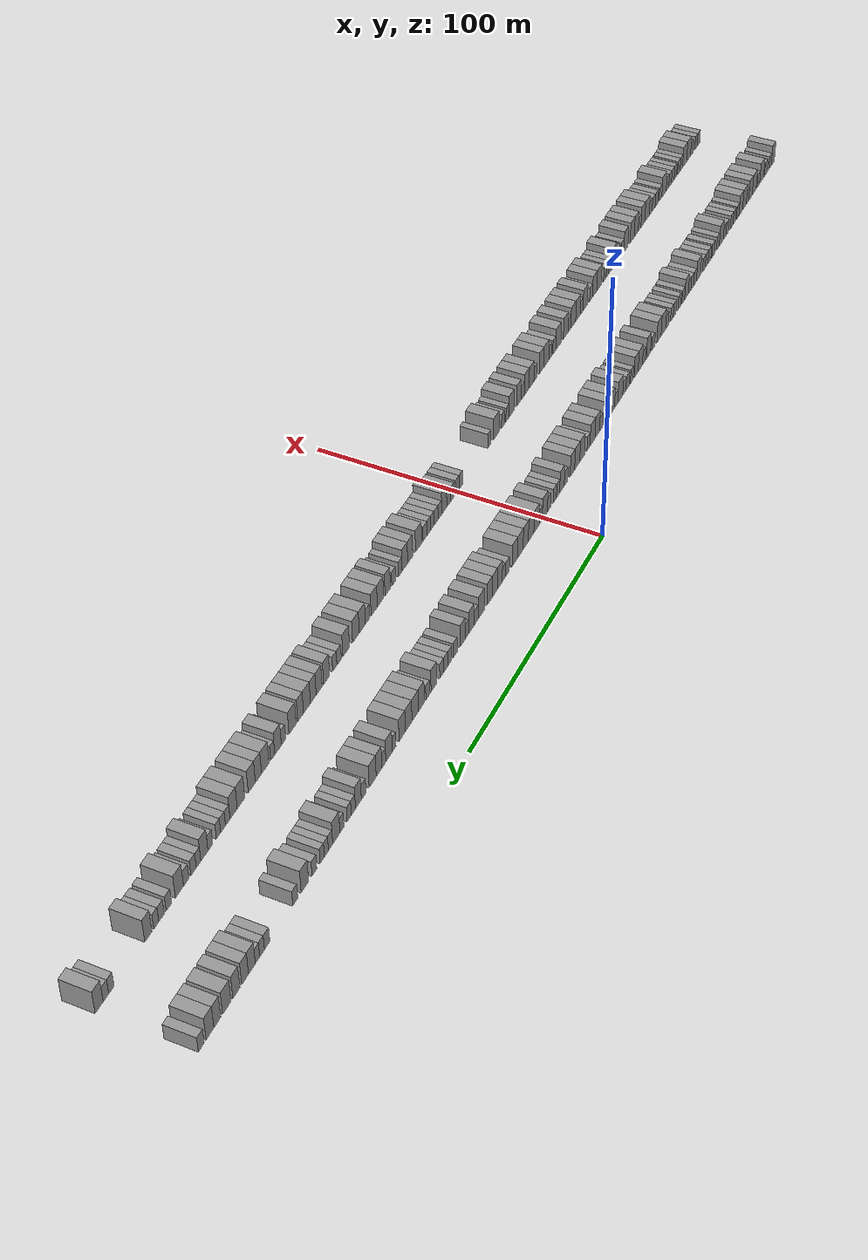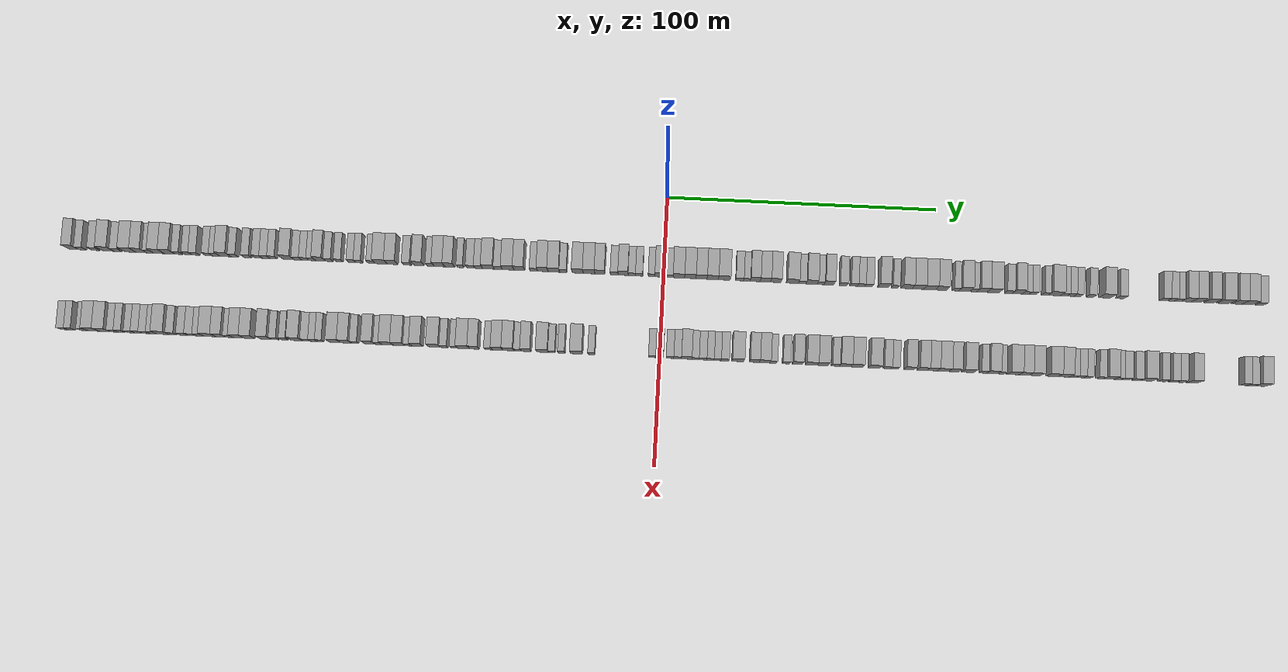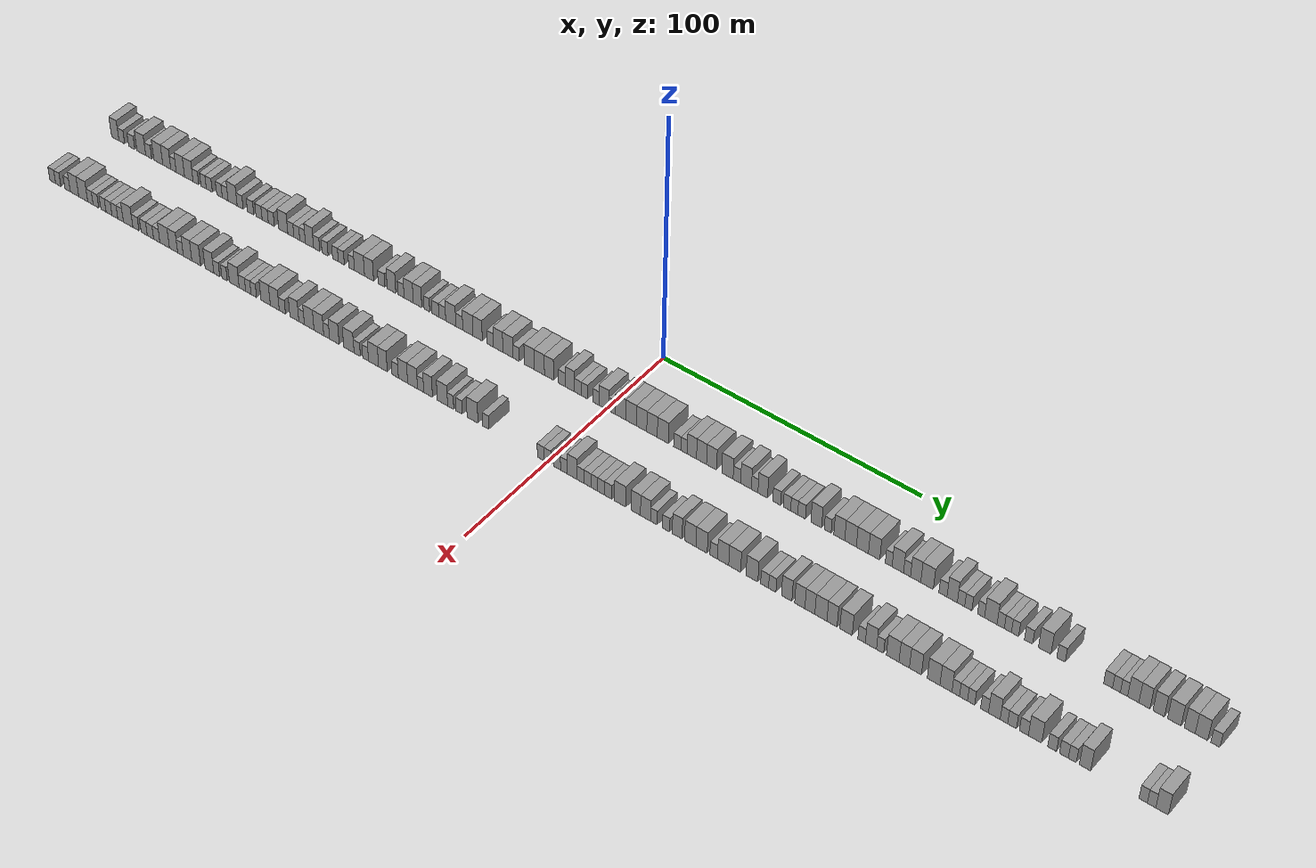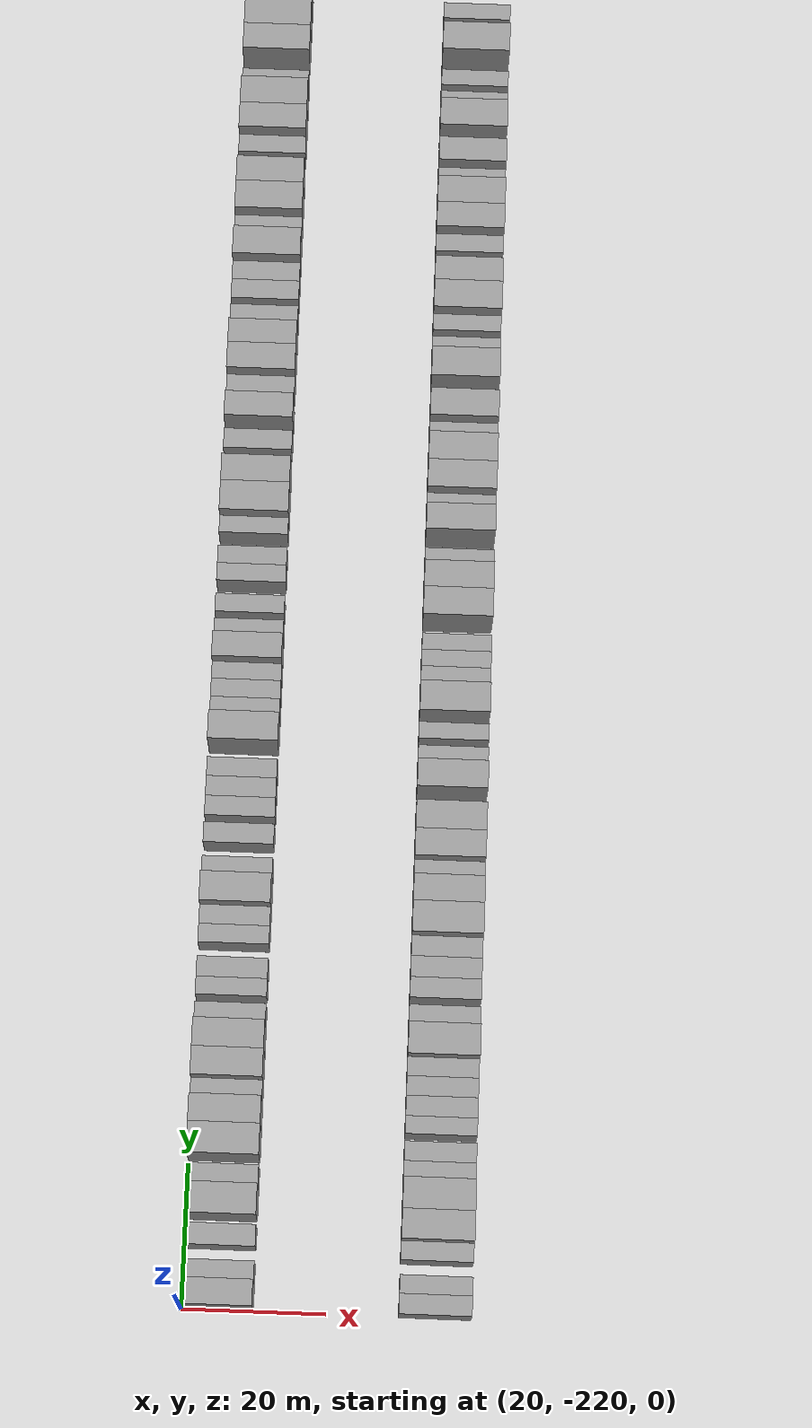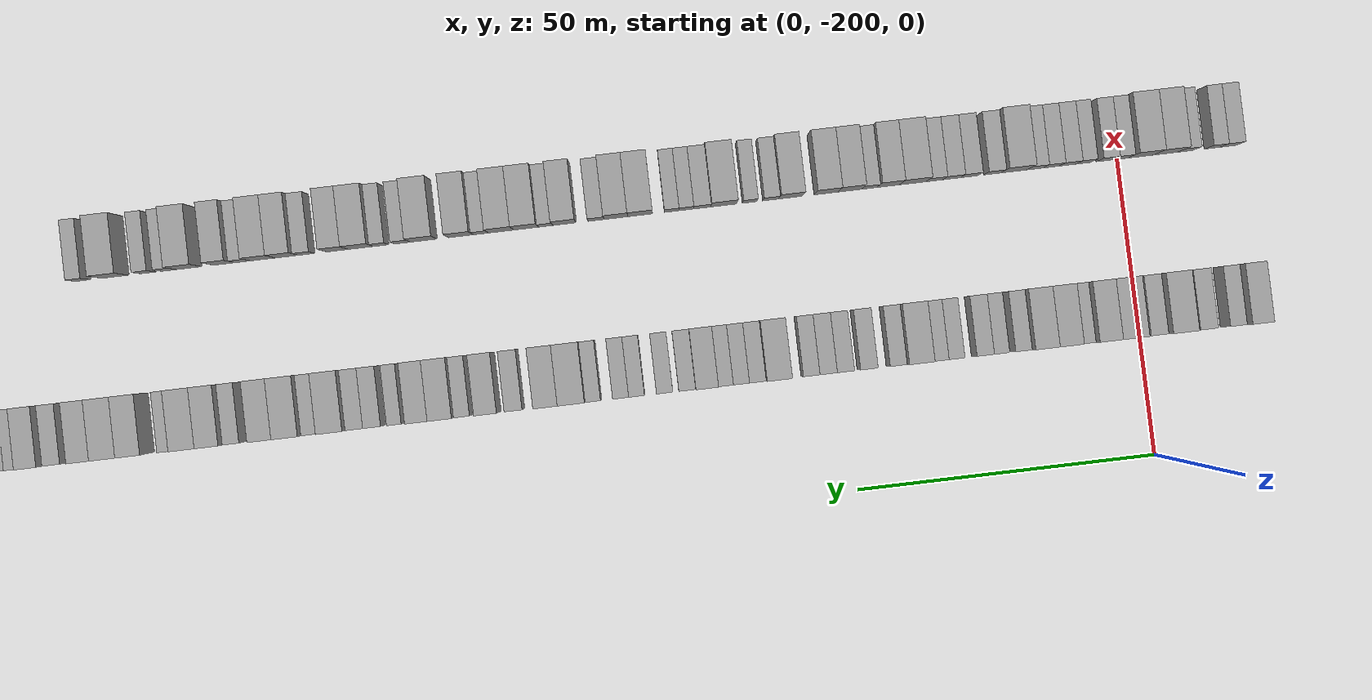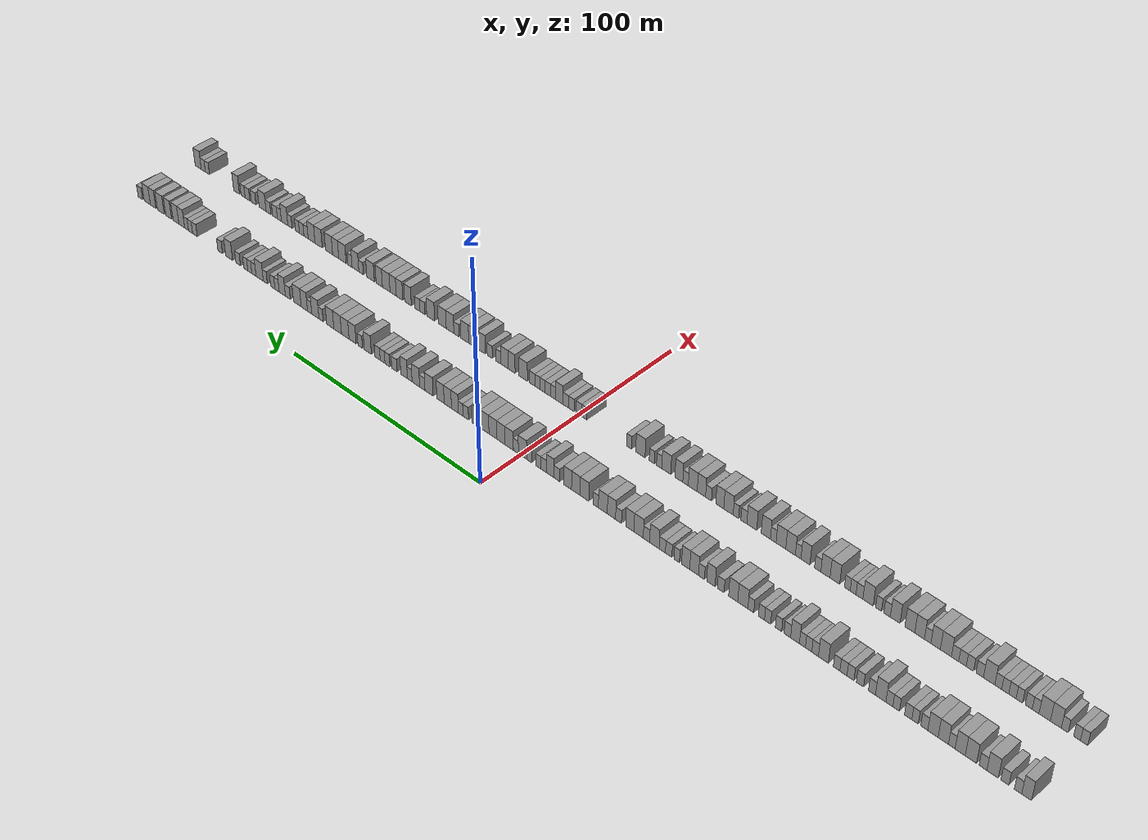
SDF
<sdf version="1.6">
 <world name="default">
  <scene>
   <sky><clouds><speed>12</speed></clouds></sky>
   <ambient>0.4 0.4 0.4 1</ambient>
   <background>0.7 0.7 0.7 1</background>
   <shadows>1</shadows>
  </scene>
  <gravity>0 0 -9.8066</gravity>
  <magnetic_field>6e-06 2.3e-05 -4.2e-05</magnetic_field>
  <physics default="0" name="default_physics" type="ode">
   <ode>
    <solver>
     <type>quick</type>
     <iters>10</iters>
     <sor>1.0</sor>
     <use_dynamic_moi_rescaling>0</use_dynamic_moi_rescaling>
    </solver>
    <constraints>
     <cfm>0</cfm>
     <erp>0.2</erp>
     <contact_max_correcting_vel>100</contact_max_correcting_vel>
     <contact_surface_layer>0.001</contact_surface_layer>
    </constraints>
   </ode>
   <max_step_size>0.004</max_step_size>
   <real_time_factor>1</real_time_factor>
   <real_time_update_rate>250</real_time_update_rate>
  </physics>
  <light name="sun" type="directional">
   <pose>0 0 10 0 0 0</pose>
   <diffuse>0.8 0.8 0.8 1</diffuse>
   <specular>0.2 0.2 0.2 1</specular>
   <attenuation>
    <range>1000</range>
    <constant>0.9</constant>
    <linear>0.01</linear>
    <quadratic>0.001</quadratic>
   </attenuation>
   <direction>-0.5 0.1 -0.9</direction>
  </light>
  <model name="building_1">
   <static>1</static>
   <pose>25.0000 -218.1999 0 0.000000 0.000000 0.000000</pose>
   <link name="link">
    <pose>0 0 4.50 0 0 0</pose>
    <collision name="collision"><geometry><box><size>10.0000 3.6002 9.0000</size></box></geometry></collision>
    <visual name="visual">
     <cast_shadows>0</cast_shadows>
     <geometry><box><size>10.0000 3.6002 9.0000</size></box></geometry>
     <material>
      <script>
       <uri>model://grey_wall/materials/scripts</uri>
       <uri>model://grey_wall/materials/textures</uri>
       <name>vrc/grey_wall</name>
      </script>
     </material>
    </visual>
   </link>
  </model>
  <model name="building_2">
   <static>1</static>
   <pose>25.0000 -215.0210 0 0.000000 0.000000 0.000000</pose>
   <link name="link">
    <pose>0 0 3.00 0 0 0</pose>
    <collision name="collision"><geometry><box><size>10.0000 2.7577 6.0000</size></box></geometry></collision>
    <visual name="visual">
     <cast_shadows>0</cast_shadows>
     <geometry><box><size>10.0000 2.7577 6.0000</size></box></geometry>
     <material>
      <script>
       <uri>model://grey_wall/materials/scripts</uri>
       <uri>model://grey_wall/materials/textures</uri>
       <name>vrc/grey_wall</name>
      </script>
     </material>
    </visual>
   </link>
  </model>
  <model name="building_3">
   <static>1</static>
   <pose>25.0000 -210.1481 0 0.000000 0.000000 0.000000</pose>
   <link name="link">
    <pose>0 0 3.00 0 0 0</pose>
    <collision name="collision"><geometry><box><size>10.0000 2.9882 6.0000</size></box></geometry></collision>
    <visual name="visual">
     <cast_shadows>0</cast_shadows>
     <geometry><box><size>10.0000 2.9882 6.0000</size></box></geometry>
     <material>
      <script>
       <uri>model://grey_wall/materials/scripts</uri>
       <uri>model://grey_wall/materials/textures</uri>
       <name>vrc/grey_wall</name>
      </script>
     </material>
    </visual>
   </link>
  </model>
  <model name="building_4">
   <static>1</static>
   <pose>25.0000 -205.5099 0 0.000000 0.000000 0.000000</pose>
   <link name="link">
    <pose>0 0 4.50 0 0 0</pose>
    <collision name="collision"><geometry><box><size>10.0000 4.2882 9.0000</size></box></geometry></collision>
    <visual name="visual">
     <cast_shadows>0</cast_shadows>
     <geometry><box><size>10.0000 4.2882 9.0000</size></box></geometry>
     <material>
      <script>
       <uri>model://grey_wall/materials/scripts</uri>
       <uri>model://grey_wall/materials/textures</uri>
       <name>vrc/grey_wall</name>
      </script>
     </material>
    </visual>
   </link>
  </model>
  <model name="building_5">
   <static>1</static>
   <pose>25.0000 -201.9123 0 0.000000 0.000000 0.000000</pose>
   <link name="link">
    <pose>0 0 3.00 0 0 0</pose>
    <collision name="collision"><geometry><box><size>10.0000 2.9070 6.0000</size></box></geometry></collision>
    <visual name="visual">
     <cast_shadows>0</cast_shadows>
     <geometry><box><size>10.0000 2.9070 6.0000</size></box></geometry>
     <material>
      <script>
       <uri>model://grey_wall/materials/scripts</uri>
       <uri>model://grey_wall/materials/textures</uri>
       <name>vrc/grey_wall</name>
      </script>
     </material>
    </visual>
   </link>
  </model>
  <model name="building_6">
   <static>1</static>
   <pose>25.0000 -197.2956 0 0.000000 0.000000 0.000000</pose>
   <link name="link">
    <pose>0 0 4.50 0 0 0</pose>
    <collision name="collision"><geometry><box><size>10.0000 4.3263 9.0000</size></box></geometry></collision>
    <visual name="visual">
     <cast_shadows>0</cast_shadows>
     <geometry><box><size>10.0000 4.3263 9.0000</size></box></geometry>
     <material>
      <script>
       <uri>model://grey_wall/materials/scripts</uri>
       <uri>model://grey_wall/materials/textures</uri>
       <name>vrc/grey_wall</name>
      </script>
     </material>
    </visual>
   </link>
  </model>
  <model name="building_7">
   <static>1</static>
   <pose>25.0000 -193.2080 0 0.000000 0.000000 0.000000</pose>
   <link name="link">
    <pose>0 0 4.50 0 0 0</pose>
    <collision name="collision"><geometry><box><size>10.0000 3.8490 9.0000</size></box></geometry></collision>
    <visual name="visual">
     <cast_shadows>0</cast_shadows>
     <geometry><box><size>10.0000 3.8490 9.0000</size></box></geometry>
     <material>
      <script>
       <uri>model://grey_wall/materials/scripts</uri>
       <uri>model://grey_wall/materials/textures</uri>
       <name>vrc/grey_wall</name>
      </script>
     </material>
    </visual>
   </link>
  </model>
  <model name="building_8">
   <static>1</static>
   <pose>25.0000 -189.9896 0 0.000000 0.000000 0.000000</pose>
   <link name="link">
    <pose>0 0 3.00 0 0 0</pose>
    <collision name="collision"><geometry><box><size>10.0000 2.5877 6.0000</size></box></geometry></collision>
    <visual name="visual">
     <cast_shadows>0</cast_shadows>
     <geometry><box><size>10.0000 2.5877 6.0000</size></box></geometry>
     <material>
      <script>
       <uri>model://grey_wall/materials/scripts</uri>
       <uri>model://grey_wall/materials/textures</uri>
       <name>vrc/grey_wall</name>
      </script>
     </material>
    </visual>
   </link>
  </model>
  <model name="building_9">
   <static>1</static>
   <pose>25.0000 -186.7082 0 0.000000 0.000000 0.000000</pose>
   <link name="link">
    <pose>0 0 4.50 0 0 0</pose>
    <collision name="collision"><geometry><box><size>10.0000 3.9751 9.0000</size></box></geometry></collision>
    <visual name="visual">
     <cast_shadows>0</cast_shadows>
     <geometry><box><size>10.0000 3.9751 9.0000</size></box></geometry>
     <material>
      <script>
       <uri>model://grey_wall/materials/scripts</uri>
       <uri>model://grey_wall/materials/textures</uri>
       <name>vrc/grey_wall</name>
      </script>
     </material>
    </visual>
   </link>
  </model>
  <model name="building_10">
   <static>1</static>
   <pose>25.0000 -182.7124 0 0.000000 0.000000 0.000000</pose>
   <link name="link">
    <pose>0 0 4.50 0 0 0</pose>
    <collision name="collision"><geometry><box><size>10.0000 4.0163 9.0000</size></box></geometry></collision>
    <visual name="visual">
     <cast_shadows>0</cast_shadows>
     <geometry><box><size>10.0000 4.0163 9.0000</size></box></geometry>
     <material>
      <script>
       <uri>model://grey_wall/materials/scripts</uri>
       <uri>model://grey_wall/materials/textures</uri>
       <name>vrc/grey_wall</name>
      </script>
     </material>
    </visual>
   </link>
  </model>
  <model name="building_11">
   <static>1</static>
   <pose>25.0000 -179.3322 0 0.000000 0.000000 0.000000</pose>
   <link name="link">
    <pose>0 0 3.00 0 0 0</pose>
    <collision name="collision"><geometry><box><size>10.0000 2.7441 6.0000</size></box></geometry></collision>
    <visual name="visual">
     <cast_shadows>0</cast_shadows>
     <geometry><box><size>10.0000 2.7441 6.0000</size></box></geometry>
     <material>
      <script>
       <uri>model://grey_wall/materials/scripts</uri>
       <uri>model://grey_wall/materials/textures</uri>
       <name>vrc/grey_wall</name>
      </script>
     </material>
    </visual>
   </link>
  </model>
  <model name="building_12">
   <static>1</static>
   <pose>25.0000 -175.6917 0 0.000000 0.000000 0.000000</pose>
   <link name="link">
    <pose>0 0 3.00 0 0 0</pose>
    <collision name="collision"><geometry><box><size>10.0000 2.5370 6.0000</size></box></geometry></collision>
    <visual name="visual">
     <cast_shadows>0</cast_shadows>
     <geometry><box><size>10.0000 2.5370 6.0000</size></box></geometry>
     <material>
      <script>
       <uri>model://grey_wall/materials/scripts</uri>
       <uri>model://grey_wall/materials/textures</uri>
       <name>vrc/grey_wall</name>
      </script>
     </material>
    </visual>
   </link>
  </model>
  <model name="building_13">
   <static>1</static>
   <pose>25.0000 -172.9795 0 0.000000 0.000000 0.000000</pose>
   <link name="link">
    <pose>0 0 3.00 0 0 0</pose>
    <collision name="collision"><geometry><box><size>10.0000 2.8872 6.0000</size></box></geometry></collision>
    <visual name="visual">
     <cast_shadows>0</cast_shadows>
     <geometry><box><size>10.0000 2.8872 6.0000</size></box></geometry>
     <material>
      <script>
       <uri>model://grey_wall/materials/scripts</uri>
       <uri>model://grey_wall/materials/textures</uri>
       <name>vrc/grey_wall</name>
      </script>
     </material>
    </visual>
   </link>
  </model>
  <model name="building_14">
   <static>1</static>
   <pose>25.0000 -168.2196 0 0.000000 0.000000 0.000000</pose>
   <link name="link">
    <pose>0 0 3.00 0 0 0</pose>
    <collision name="collision"><geometry><box><size>10.0000 2.6327 6.0000</size></box></geometry></collision>
    <visual name="visual">
     <cast_shadows>0</cast_shadows>
     <geometry><box><size>10.0000 2.6327 6.0000</size></box></geometry>
     <material>
      <script>
       <uri>model://grey_wall/materials/scripts</uri>
       <uri>model://grey_wall/materials/textures</uri>
       <name>vrc/grey_wall</name>
      </script>
     </material>
    </visual>
   </link>
  </model>
  <model name="building_15">
   <static>1</static>
   <pose>25.0000 -165.5320 0 0.000000 0.000000 0.000000</pose>
   <link name="link">
    <pose>0 0 3.00 0 0 0</pose>
    <collision name="collision"><geometry><box><size>10.0000 2.7424 6.0000</size></box></geometry></collision>
    <visual name="visual">
     <cast_shadows>0</cast_shadows>
     <geometry><box><size>10.0000 2.7424 6.0000</size></box></geometry>
     <material>
      <script>
       <uri>model://grey_wall/materials/scripts</uri>
       <uri>model://grey_wall/materials/textures</uri>
       <name>vrc/grey_wall</name>
      </script>
     </material>
    </visual>
   </link>
  </model>
  <model name="building_16">
   <static>1</static>
   <pose>25.0000 -162.0608 0 0.000000 0.000000 0.000000</pose>
   <link name="link">
    <pose>0 0 4.50 0 0 0</pose>
    <collision name="collision"><geometry><box><size>10.0000 4.2000 9.0000</size></box></geometry></collision>
    <visual name="visual">
     <cast_shadows>0</cast_shadows>
     <geometry><box><size>10.0000 4.2000 9.0000</size></box></geometry>
     <material>
      <script>
       <uri>model://grey_wall/materials/scripts</uri>
       <uri>model://grey_wall/materials/textures</uri>
       <name>vrc/grey_wall</name>
      </script>
     </material>
    </visual>
   </link>
  </model>
  <model name="building_17">
   <static>1</static>
   <pose>25.0000 -158.5487 0 0.000000 0.000000 0.000000</pose>
   <link name="link">
    <pose>0 0 3.00 0 0 0</pose>
    <collision name="collision"><geometry><box><size>10.0000 2.8243 6.0000</size></box></geometry></collision>
    <visual name="visual">
     <cast_shadows>0</cast_shadows>
     <geometry><box><size>10.0000 2.8243 6.0000</size></box></geometry>
     <material>
      <script>
       <uri>model://grey_wall/materials/scripts</uri>
       <uri>model://grey_wall/materials/textures</uri>
       <name>vrc/grey_wall</name>
      </script>
     </material>
    </visual>
   </link>
  </model>
  <model name="building_18">
   <static>1</static>
   <pose>25.0000 -153.6784 0 0.000000 0.000000 0.000000</pose>
   <link name="link">
    <pose>0 0 3.00 0 0 0</pose>
    <collision name="collision"><geometry><box><size>10.0000 2.9164 6.0000</size></box></geometry></collision>
    <visual name="visual">
     <cast_shadows>0</cast_shadows>
     <geometry><box><size>10.0000 2.9164 6.0000</size></box></geometry>
     <material>
      <script>
       <uri>model://grey_wall/materials/scripts</uri>
       <uri>model://grey_wall/materials/textures</uri>
       <name>vrc/grey_wall</name>
      </script>
     </material>
    </visual>
   </link>
  </model>
  <model name="building_19">
   <static>1</static>
   <pose>25.0000 -149.7978 0 0.000000 0.000000 0.000000</pose>
   <link name="link">
    <pose>0 0 3.00 0 0 0</pose>
    <collision name="collision"><geometry><box><size>10.0000 2.8447 6.0000</size></box></geometry></collision>
    <visual name="visual">
     <cast_shadows>0</cast_shadows>
     <geometry><box><size>10.0000 2.8447 6.0000</size></box></geometry>
     <material>
      <script>
       <uri>model://grey_wall/materials/scripts</uri>
       <uri>model://grey_wall/materials/textures</uri>
       <name>vrc/grey_wall</name>
      </script>
     </material>
    </visual>
   </link>
  </model>
  <model name="building_20">
   <static>1</static>
   <pose>25.0000 -146.9316 0 0.000000 0.000000 0.000000</pose>
   <link name="link">
    <pose>0 0 3.00 0 0 0</pose>
    <collision name="collision"><geometry><box><size>10.0000 2.8878 6.0000</size></box></geometry></collision>
    <visual name="visual">
     <cast_shadows>0</cast_shadows>
     <geometry><box><size>10.0000 2.8878 6.0000</size></box></geometry>
     <material>
      <script>
       <uri>model://grey_wall/materials/scripts</uri>
       <uri>model://grey_wall/materials/textures</uri>
       <name>vrc/grey_wall</name>
      </script>
     </material>
    </visual>
   </link>
  </model>
  <model name="building_21">
   <static>1</static>
   <pose>25.0000 -144.1135 0 0.000000 0.000000 0.000000</pose>
   <link name="link">
    <pose>0 0 3.00 0 0 0</pose>
    <collision name="collision"><geometry><box><size>10.0000 2.7484 6.0000</size></box></geometry></collision>
    <visual name="visual">
     <cast_shadows>0</cast_shadows>
     <geometry><box><size>10.0000 2.7484 6.0000</size></box></geometry>
     <material>
      <script>
       <uri>model://grey_wall/materials/scripts</uri>
       <uri>model://grey_wall/materials/textures</uri>
       <name>vrc/grey_wall</name>
      </script>
     </material>
    </visual>
   </link>
  </model>
  <model name="building_22">
   <static>1</static>
   <pose>25.0000 -138.6592 0 0.000000 0.000000 0.000000</pose>
   <link name="link">
    <pose>0 0 4.50 0 0 0</pose>
    <collision name="collision"><geometry><box><size>10.0000 4.1602 9.0000</size></box></geometry></collision>
    <visual name="visual">
     <cast_shadows>0</cast_shadows>
     <geometry><box><size>10.0000 4.1602 9.0000</size></box></geometry>
     <material>
      <script>
       <uri>model://grey_wall/materials/scripts</uri>
       <uri>model://grey_wall/materials/textures</uri>
       <name>vrc/grey_wall</name>
      </script>
     </material>
    </visual>
   </link>
  </model>
  <model name="building_23">
   <static>1</static>
   <pose>25.0000 -135.1899 0 0.000000 0.000000 0.000000</pose>
   <link name="link">
    <pose>0 0 3.00 0 0 0</pose>
    <collision name="collision"><geometry><box><size>10.0000 2.7784 6.0000</size></box></geometry></collision>
    <visual name="visual">
     <cast_shadows>0</cast_shadows>
     <geometry><box><size>10.0000 2.7784 6.0000</size></box></geometry>
     <material>
      <script>
       <uri>model://grey_wall/materials/scripts</uri>
       <uri>model://grey_wall/materials/textures</uri>
       <name>vrc/grey_wall</name>
      </script>
     </material>
    </visual>
   </link>
  </model>
  <model name="building_24">
   <static>1</static>
   <pose>25.0000 -132.4624 0 0.000000 0.000000 0.000000</pose>
   <link name="link">
    <pose>0 0 3.00 0 0 0</pose>
    <collision name="collision"><geometry><box><size>10.0000 2.6766 6.0000</size></box></geometry></collision>
    <visual name="visual">
     <cast_shadows>0</cast_shadows>
     <geometry><box><size>10.0000 2.6766 6.0000</size></box></geometry>
     <material>
      <script>
       <uri>model://grey_wall/materials/scripts</uri>
       <uri>model://grey_wall/materials/textures</uri>
       <name>vrc/grey_wall</name>
      </script>
     </material>
    </visual>
   </link>
  </model>
  <model name="building_25">
   <static>1</static>
   <pose>25.0000 -129.8567 0 0.000000 0.000000 0.000000</pose>
   <link name="link">
    <pose>0 0 3.00 0 0 0</pose>
    <collision name="collision"><geometry><box><size>10.0000 2.5349 6.0000</size></box></geometry></collision>
    <visual name="visual">
     <cast_shadows>0</cast_shadows>
     <geometry><box><size>10.0000 2.5349 6.0000</size></box></geometry>
     <material>
      <script>
       <uri>model://grey_wall/materials/scripts</uri>
       <uri>model://grey_wall/materials/textures</uri>
       <name>vrc/grey_wall</name>
      </script>
     </material>
    </visual>
   </link>
  </model>
  <model name="building_26">
   <static>1</static>
   <pose>25.0000 -126.7291 0 0.000000 0.000000 0.000000</pose>
   <link name="link">
    <pose>0 0 4.50 0 0 0</pose>
    <collision name="collision"><geometry><box><size>10.0000 3.7203 9.0000</size></box></geometry></collision>
    <visual name="visual">
     <cast_shadows>0</cast_shadows>
     <geometry><box><size>10.0000 3.7203 9.0000</size></box></geometry>
     <material>
      <script>
       <uri>model://grey_wall/materials/scripts</uri>
       <uri>model://grey_wall/materials/textures</uri>
       <name>vrc/grey_wall</name>
      </script>
     </material>
    </visual>
   </link>
  </model>
  <model name="building_27">
   <static>1</static>
   <pose>25.0000 -123.4725 0 0.000000 0.000000 0.000000</pose>
   <link name="link">
    <pose>0 0 3.00 0 0 0</pose>
    <collision name="collision"><geometry><box><size>10.0000 2.7929 6.0000</size></box></geometry></collision>
    <visual name="visual">
     <cast_shadows>0</cast_shadows>
     <geometry><box><size>10.0000 2.7929 6.0000</size></box></geometry>
     <material>
      <script>
       <uri>model://grey_wall/materials/scripts</uri>
       <uri>model://grey_wall/materials/textures</uri>
       <name>vrc/grey_wall</name>
      </script>
     </material>
    </visual>
   </link>
  </model>
  <model name="building_28">
   <static>1</static>
   <pose>25.0000 -119.7247 0 0.000000 0.000000 0.000000</pose>
   <link name="link">
    <pose>0 0 3.00 0 0 0</pose>
    <collision name="collision"><geometry><box><size>10.0000 2.7026 6.0000</size></box></geometry></collision>
    <visual name="visual">
     <cast_shadows>0</cast_shadows>
     <geometry><box><size>10.0000 2.7026 6.0000</size></box></geometry>
     <material>
      <script>
       <uri>model://grey_wall/materials/scripts</uri>
       <uri>model://grey_wall/materials/textures</uri>
       <name>vrc/grey_wall</name>
      </script>
     </material>
    </visual>
   </link>
  </model>
  <model name="building_29">
   <static>1</static>
   <pose>25.0000 -115.0625 0 0.000000 0.000000 0.000000</pose>
   <link name="link">
    <pose>0 0 3.00 0 0 0</pose>
    <collision name="collision"><geometry><box><size>10.0000 2.6219 6.0000</size></box></geometry></collision>
    <visual name="visual">
     <cast_shadows>0</cast_shadows>
     <geometry><box><size>10.0000 2.6219 6.0000</size></box></geometry>
     <material>
      <script>
       <uri>model://grey_wall/materials/scripts</uri>
       <uri>model://grey_wall/materials/textures</uri>
       <name>vrc/grey_wall</name>
      </script>
     </material>
    </visual>
   </link>
  </model>
  <model name="building_30">
   <static>1</static>
   <pose>25.0000 -112.4210 0 0.000000 0.000000 0.000000</pose>
   <link name="link">
    <pose>0 0 3.00 0 0 0</pose>
    <collision name="collision"><geometry><box><size>10.0000 2.6610 6.0000</size></box></geometry></collision>
    <visual name="visual">
     <cast_shadows>0</cast_shadows>
     <geometry><box><size>10.0000 2.6610 6.0000</size></box></geometry>
     <material>
      <script>
       <uri>model://grey_wall/materials/scripts</uri>
       <uri>model://grey_wall/materials/textures</uri>
       <name>vrc/grey_wall</name>
      </script>
     </material>
    </visual>
   </link>
  </model>
  <model name="building_31">
   <static>1</static>
   <pose>25.0000 -107.8168 0 0.000000 0.000000 0.000000</pose>
   <link name="link">
    <pose>0 0 3.00 0 0 0</pose>
    <collision name="collision"><geometry><box><size>10.0000 2.5475 6.0000</size></box></geometry></collision>
    <visual name="visual">
     <cast_shadows>0</cast_shadows>
     <geometry><box><size>10.0000 2.5475 6.0000</size></box></geometry>
     <material>
      <script>
       <uri>model://grey_wall/materials/scripts</uri>
       <uri>model://grey_wall/materials/textures</uri>
       <name>vrc/grey_wall</name>
      </script>
     </material>
    </visual>
   </link>
  </model>
  <model name="building_32">
   <static>1</static>
   <pose>25.0000 -104.3199 0 0.000000 0.000000 0.000000</pose>
   <link name="link">
    <pose>0 0 4.50 0 0 0</pose>
    <collision name="collision"><geometry><box><size>10.0000 4.4463 9.0000</size></box></geometry></collision>
    <visual name="visual">
     <cast_shadows>0</cast_shadows>
     <geometry><box><size>10.0000 4.4463 9.0000</size></box></geometry>
     <material>
      <script>
       <uri>model://grey_wall/materials/scripts</uri>
       <uri>model://grey_wall/materials/textures</uri>
       <name>vrc/grey_wall</name>
      </script>
     </material>
    </visual>
   </link>
  </model>
  <model name="building_33">
   <static>1</static>
   <pose>25.0000 -100.0908 0 0.000000 0.000000 0.000000</pose>
   <link name="link">
    <pose>0 0 4.50 0 0 0</pose>
    <collision name="collision"><geometry><box><size>10.0000 4.0121 9.0000</size></box></geometry></collision>
    <visual name="visual">
     <cast_shadows>0</cast_shadows>
     <geometry><box><size>10.0000 4.0121 9.0000</size></box></geometry>
     <material>
      <script>
       <uri>model://grey_wall/materials/scripts</uri>
       <uri>model://grey_wall/materials/textures</uri>
       <name>vrc/grey_wall</name>
      </script>
     </material>
    </visual>
   </link>
  </model>
  <model name="building_34">
   <static>1</static>
   <pose>25.0000 -94.5969 0 0.000000 0.000000 0.000000</pose>
   <link name="link">
    <pose>0 0 3.00 0 0 0</pose>
    <collision name="collision"><geometry><box><size>10.0000 2.9756 6.0000</size></box></geometry></collision>
    <visual name="visual">
     <cast_shadows>0</cast_shadows>
     <geometry><box><size>10.0000 2.9756 6.0000</size></box></geometry>
     <material>
      <script>
       <uri>model://grey_wall/materials/scripts</uri>
       <uri>model://grey_wall/materials/textures</uri>
       <name>vrc/grey_wall</name>
      </script>
     </material>
    </visual>
   </link>
  </model>
  <model name="building_35">
   <static>1</static>
   <pose>25.0000 -90.2380 0 0.000000 0.000000 0.000000</pose>
   <link name="link">
    <pose>0 0 4.50 0 0 0</pose>
    <collision name="collision"><geometry><box><size>10.0000 3.7423 9.0000</size></box></geometry></collision>
    <visual name="visual">
     <cast_shadows>0</cast_shadows>
     <geometry><box><size>10.0000 3.7423 9.0000</size></box></geometry>
     <material>
      <script>
       <uri>model://grey_wall/materials/scripts</uri>
       <uri>model://grey_wall/materials/textures</uri>
       <name>vrc/grey_wall</name>
      </script>
     </material>
    </visual>
   </link>
  </model>
  <model name="building_36">
   <static>1</static>
   <pose>25.0000 -86.0465 0 0.000000 0.000000 0.000000</pose>
   <link name="link">
    <pose>0 0 3.00 0 0 0</pose>
    <collision name="collision"><geometry><box><size>10.0000 2.6405 6.0000</size></box></geometry></collision>
    <visual name="visual">
     <cast_shadows>0</cast_shadows>
     <geometry><box><size>10.0000 2.6405 6.0000</size></box></geometry>
     <material>
      <script>
       <uri>model://grey_wall/materials/scripts</uri>
       <uri>model://grey_wall/materials/textures</uri>
       <name>vrc/grey_wall</name>
      </script>
     </material>
    </visual>
   </link>
  </model>
  <model name="building_37">
   <static>1</static>
   <pose>25.0000 -82.7317 0 0.000000 0.000000 0.000000</pose>
   <link name="link">
    <pose>0 0 4.50 0 0 0</pose>
    <collision name="collision"><geometry><box><size>10.0000 3.9891 9.0000</size></box></geometry></collision>
    <visual name="visual">
     <cast_shadows>0</cast_shadows>
     <geometry><box><size>10.0000 3.9891 9.0000</size></box></geometry>
     <material>
      <script>
       <uri>model://grey_wall/materials/scripts</uri>
       <uri>model://grey_wall/materials/textures</uri>
       <name>vrc/grey_wall</name>
      </script>
     </material>
    </visual>
   </link>
  </model>
  <model name="building_38">
   <static>1</static>
   <pose>25.0000 -78.8998 0 0.000000 0.000000 0.000000</pose>
   <link name="link">
    <pose>0 0 4.50 0 0 0</pose>
    <collision name="collision"><geometry><box><size>10.0000 3.6748 9.0000</size></box></geometry></collision>
    <visual name="visual">
     <cast_shadows>0</cast_shadows>
     <geometry><box><size>10.0000 3.6748 9.0000</size></box></geometry>
     <material>
      <script>
       <uri>model://grey_wall/materials/scripts</uri>
       <uri>model://grey_wall/materials/textures</uri>
       <name>vrc/grey_wall</name>
      </script>
     </material>
    </visual>
   </link>
  </model>
  <model name="building_39">
   <static>1</static>
   <pose>25.0000 -74.8521 0 0.000000 0.000000 0.000000</pose>
   <link name="link">
    <pose>0 0 3.00 0 0 0</pose>
    <collision name="collision"><geometry><box><size>10.0000 2.4206 6.0000</size></box></geometry></collision>
    <visual name="visual">
     <cast_shadows>0</cast_shadows>
     <geometry><box><size>10.0000 2.4206 6.0000</size></box></geometry>
     <material>
      <script>
       <uri>model://grey_wall/materials/scripts</uri>
       <uri>model://grey_wall/materials/textures</uri>
       <name>vrc/grey_wall</name>
      </script>
     </material>
    </visual>
   </link>
  </model>
  <model name="building_40">
   <static>1</static>
   <pose>25.0000 -71.1641 0 0.000000 0.000000 0.000000</pose>
   <link name="link">
    <pose>0 0 3.00 0 0 0</pose>
    <collision name="collision"><geometry><box><size>10.0000 2.9554 6.0000</size></box></geometry></collision>
    <visual name="visual">
     <cast_shadows>0</cast_shadows>
     <geometry><box><size>10.0000 2.9554 6.0000</size></box></geometry>
     <material>
      <script>
       <uri>model://grey_wall/materials/scripts</uri>
       <uri>model://grey_wall/materials/textures</uri>
       <name>vrc/grey_wall</name>
      </script>
     </material>
    </visual>
   </link>
  </model>
  <model name="building_41">
   <static>1</static>
   <pose>25.0000 -68.2301 0 0.000000 0.000000 0.000000</pose>
   <link name="link">
    <pose>0 0 3.00 0 0 0</pose>
    <collision name="collision"><geometry><box><size>10.0000 2.9125 6.0000</size></box></geometry></collision>
    <visual name="visual">
     <cast_shadows>0</cast_shadows>
     <geometry><box><size>10.0000 2.9125 6.0000</size></box></geometry>
     <material>
      <script>
       <uri>model://grey_wall/materials/scripts</uri>
       <uri>model://grey_wall/materials/textures</uri>
       <name>vrc/grey_wall</name>
      </script>
     </material>
    </visual>
   </link>
  </model>
  <model name="building_42">
   <static>1</static>
   <pose>25.0000 -64.6002 0 0.000000 0.000000 0.000000</pose>
   <link name="link">
    <pose>0 0 4.50 0 0 0</pose>
    <collision name="collision"><geometry><box><size>10.0000 4.3473 9.0000</size></box></geometry></collision>
    <visual name="visual">
     <cast_shadows>0</cast_shadows>
     <geometry><box><size>10.0000 4.3473 9.0000</size></box></geometry>
     <material>
      <script>
       <uri>model://grey_wall/materials/scripts</uri>
       <uri>model://grey_wall/materials/textures</uri>
       <name>vrc/grey_wall</name>
      </script>
     </material>
    </visual>
   </link>
  </model>
  <model name="building_43">
   <static>1</static>
   <pose>25.0000 -60.9436 0 0.000000 0.000000 0.000000</pose>
   <link name="link">
    <pose>0 0 3.00 0 0 0</pose>
    <collision name="collision"><geometry><box><size>10.0000 2.9658 6.0000</size></box></geometry></collision>
    <visual name="visual">
     <cast_shadows>0</cast_shadows>
     <geometry><box><size>10.0000 2.9658 6.0000</size></box></geometry>
     <material>
      <script>
       <uri>model://grey_wall/materials/scripts</uri>
       <uri>model://grey_wall/materials/textures</uri>
       <name>vrc/grey_wall</name>
      </script>
     </material>
    </visual>
   </link>
  </model>
  <model name="building_44">
   <static>1</static>
   <pose>25.0000 -57.2995 0 0.000000 0.000000 0.000000</pose>
   <link name="link">
    <pose>0 0 4.50 0 0 0</pose>
    <collision name="collision"><geometry><box><size>10.0000 4.3224 9.0000</size></box></geometry></collision>
    <visual name="visual">
     <cast_shadows>0</cast_shadows>
     <geometry><box><size>10.0000 4.3224 9.0000</size></box></geometry>
     <material>
      <script>
       <uri>model://grey_wall/materials/scripts</uri>
       <uri>model://grey_wall/materials/textures</uri>
       <name>vrc/grey_wall</name>
      </script>
     </material>
    </visual>
   </link>
  </model>
  <model name="building_45">
   <static>1</static>
   <pose>25.0000 -53.1680 0 0.000000 0.000000 0.000000</pose>
   <link name="link">
    <pose>0 0 4.50 0 0 0</pose>
    <collision name="collision"><geometry><box><size>10.0000 3.9408 9.0000</size></box></geometry></collision>
    <visual name="visual">
     <cast_shadows>0</cast_shadows>
     <geometry><box><size>10.0000 3.9408 9.0000</size></box></geometry>
     <material>
      <script>
       <uri>model://grey_wall/materials/scripts</uri>
       <uri>model://grey_wall/materials/textures</uri>
       <name>vrc/grey_wall</name>
      </script>
     </material>
    </visual>
   </link>
  </model>
  <model name="building_46">
   <static>1</static>
   <pose>25.0000 -47.8245 0 0.000000 0.000000 0.000000</pose>
   <link name="link">
    <pose>0 0 3.00 0 0 0</pose>
    <collision name="collision"><geometry><box><size>10.0000 2.7462 6.0000</size></box></geometry></collision>
    <visual name="visual">
     <cast_shadows>0</cast_shadows>
     <geometry><box><size>10.0000 2.7462 6.0000</size></box></geometry>
     <material>
      <script>
       <uri>model://grey_wall/materials/scripts</uri>
       <uri>model://grey_wall/materials/textures</uri>
       <name>vrc/grey_wall</name>
      </script>
     </material>
    </visual>
   </link>
  </model>
  <model name="building_47">
   <static>1</static>
   <pose>25.0000 -44.4998 0 0.000000 0.000000 0.000000</pose>
   <link name="link">
    <pose>0 0 4.50 0 0 0</pose>
    <collision name="collision"><geometry><box><size>10.0000 3.9032 9.0000</size></box></geometry></collision>
    <visual name="visual">
     <cast_shadows>0</cast_shadows>
     <geometry><box><size>10.0000 3.9032 9.0000</size></box></geometry>
     <material>
      <script>
       <uri>model://grey_wall/materials/scripts</uri>
       <uri>model://grey_wall/materials/textures</uri>
       <name>vrc/grey_wall</name>
      </script>
     </material>
    </visual>
   </link>
  </model>
  <model name="building_48">
   <static>1</static>
   <pose>25.0000 -40.4102 0 0.000000 0.000000 0.000000</pose>
   <link name="link">
    <pose>0 0 4.50 0 0 0</pose>
    <collision name="collision"><geometry><box><size>10.0000 4.2760 9.0000</size></box></geometry></collision>
    <visual name="visual">
     <cast_shadows>0</cast_shadows>
     <geometry><box><size>10.0000 4.2760 9.0000</size></box></geometry>
     <material>
      <script>
       <uri>model://grey_wall/materials/scripts</uri>
       <uri>model://grey_wall/materials/textures</uri>
       <name>vrc/grey_wall</name>
      </script>
     </material>
    </visual>
   </link>
  </model>
  <model name="building_49">
   <static>1</static>
   <pose>25.0000 -36.9497 0 0.000000 0.000000 0.000000</pose>
   <link name="link">
    <pose>0 0 3.00 0 0 0</pose>
    <collision name="collision"><geometry><box><size>10.0000 2.6450 6.0000</size></box></geometry></collision>
    <visual name="visual">
     <cast_shadows>0</cast_shadows>
     <geometry><box><size>10.0000 2.6450 6.0000</size></box></geometry>
     <material>
      <script>
       <uri>model://grey_wall/materials/scripts</uri>
       <uri>model://grey_wall/materials/textures</uri>
       <name>vrc/grey_wall</name>
      </script>
     </material>
    </visual>
   </link>
  </model>
  <model name="building_50">
   <static>1</static>
   <pose>25.0000 -31.5920 0 0.000000 0.000000 0.000000</pose>
   <link name="link">
    <pose>0 0 4.50 0 0 0</pose>
    <collision name="collision"><geometry><box><size>10.0000 4.0703 9.0000</size></box></geometry></collision>
    <visual name="visual">
     <cast_shadows>0</cast_shadows>
     <geometry><box><size>10.0000 4.0703 9.0000</size></box></geometry>
     <material>
      <script>
       <uri>model://grey_wall/materials/scripts</uri>
       <uri>model://grey_wall/materials/textures</uri>
       <name>vrc/grey_wall</name>
      </script>
     </material>
    </visual>
   </link>
  </model>
  <model name="building_51">
   <static>1</static>
   <pose>25.0000 -27.4132 0 0.000000 0.000000 0.000000</pose>
   <link name="link">
    <pose>0 0 4.50 0 0 0</pose>
    <collision name="collision"><geometry><box><size>10.0000 4.2873 9.0000</size></box></geometry></collision>
    <visual name="visual">
     <cast_shadows>0</cast_shadows>
     <geometry><box><size>10.0000 4.2873 9.0000</size></box></geometry>
     <material>
      <script>
       <uri>model://grey_wall/materials/scripts</uri>
       <uri>model://grey_wall/materials/textures</uri>
       <name>vrc/grey_wall</name>
      </script>
     </material>
    </visual>
   </link>
  </model>
  <model name="building_52">
   <static>1</static>
   <pose>25.0000 -23.4072 0 0.000000 0.000000 0.000000</pose>
   <link name="link">
    <pose>0 0 4.50 0 0 0</pose>
    <collision name="collision"><geometry><box><size>10.0000 3.7247 9.0000</size></box></geometry></collision>
    <visual name="visual">
     <cast_shadows>0</cast_shadows>
     <geometry><box><size>10.0000 3.7247 9.0000</size></box></geometry>
     <material>
      <script>
       <uri>model://grey_wall/materials/scripts</uri>
       <uri>model://grey_wall/materials/textures</uri>
       <name>vrc/grey_wall</name>
      </script>
     </material>
    </visual>
   </link>
  </model>
  <model name="building_53">
   <static>1</static>
   <pose>25.0000 -18.0842 0 0.000000 0.000000 0.000000</pose>
   <link name="link">
    <pose>0 0 3.00 0 0 0</pose>
    <collision name="collision"><geometry><box><size>10.0000 2.9214 6.0000</size></box></geometry></collision>
    <visual name="visual">
     <cast_shadows>0</cast_shadows>
     <geometry><box><size>10.0000 2.9214 6.0000</size></box></geometry>
     <material>
      <script>
       <uri>model://grey_wall/materials/scripts</uri>
       <uri>model://grey_wall/materials/textures</uri>
       <name>vrc/grey_wall</name>
      </script>
     </material>
    </visual>
   </link>
  </model>
  <model name="building_54">
   <static>1</static>
   <pose>25.0000 -14.7906 0 0.000000 0.000000 0.000000</pose>
   <link name="link">
    <pose>0 0 4.50 0 0 0</pose>
    <collision name="collision"><geometry><box><size>10.0000 3.6657 9.0000</size></box></geometry></collision>
    <visual name="visual">
     <cast_shadows>0</cast_shadows>
     <geometry><box><size>10.0000 3.6657 9.0000</size></box></geometry>
     <material>
      <script>
       <uri>model://grey_wall/materials/scripts</uri>
       <uri>model://grey_wall/materials/textures</uri>
       <name>vrc/grey_wall</name>
      </script>
     </material>
    </visual>
   </link>
  </model>
  <model name="building_55">
   <static>1</static>
   <pose>25.0000 -11.6053 0 0.000000 0.000000 0.000000</pose>
   <link name="link">
    <pose>0 0 3.00 0 0 0</pose>
    <collision name="collision"><geometry><box><size>10.0000 2.7048 6.0000</size></box></geometry></collision>
    <visual name="visual">
     <cast_shadows>0</cast_shadows>
     <geometry><box><size>10.0000 2.7048 6.0000</size></box></geometry>
     <material>
      <script>
       <uri>model://grey_wall/materials/scripts</uri>
       <uri>model://grey_wall/materials/textures</uri>
       <name>vrc/grey_wall</name>
      </script>
     </material>
    </visual>
   </link>
  </model>
  <model name="building_56">
   <static>1</static>
   <pose>25.0000 -8.9173 0 0.000000 0.000000 0.000000</pose>
   <link name="link">
    <pose>0 0 3.00 0 0 0</pose>
    <collision name="collision"><geometry><box><size>10.0000 2.6713 6.0000</size></box></geometry></collision>
    <visual name="visual">
     <cast_shadows>0</cast_shadows>
     <geometry><box><size>10.0000 2.6713 6.0000</size></box></geometry>
     <material>
      <script>
       <uri>model://grey_wall/materials/scripts</uri>
       <uri>model://grey_wall/materials/textures</uri>
       <name>vrc/grey_wall</name>
      </script>
     </material>
    </visual>
   </link>
  </model>
  <model name="building_57">
   <static>1</static>
   <pose>25.0000 -4.3405 0 0.000000 0.000000 0.000000</pose>
   <link name="link">
    <pose>0 0 3.00 0 0 0</pose>
    <collision name="collision"><geometry><box><size>10.0000 2.4823 6.0000</size></box></geometry></collision>
    <visual name="visual">
     <cast_shadows>0</cast_shadows>
     <geometry><box><size>10.0000 2.4823 6.0000</size></box></geometry>
     <material>
      <script>
       <uri>model://grey_wall/materials/scripts</uri>
       <uri>model://grey_wall/materials/textures</uri>
       <name>vrc/grey_wall</name>
      </script>
     </material>
    </visual>
   </link>
  </model>
  <model name="building_58">
   <static>1</static>
   <pose>25.0000 -1.0252 0 0.000000 0.000000 0.000000</pose>
   <link name="link">
    <pose>0 0 4.50 0 0 0</pose>
    <collision name="collision"><geometry><box><size>10.0000 4.1484 9.0000</size></box></geometry></collision>
    <visual name="visual">
     <cast_shadows>0</cast_shadows>
     <geometry><box><size>10.0000 4.1484 9.0000</size></box></geometry>
     <material>
      <script>
       <uri>model://grey_wall/materials/scripts</uri>
       <uri>model://grey_wall/materials/textures</uri>
       <name>vrc/grey_wall</name>
      </script>
     </material>
    </visual>
   </link>
  </model>
  <model name="building_59">
   <static>1</static>
   <pose>25.0000 2.3257 0 0.000000 0.000000 0.000000</pose>
   <link name="link">
    <pose>0 0 3.00 0 0 0</pose>
    <collision name="collision"><geometry><box><size>10.0000 2.5534 6.0000</size></box></geometry></collision>
    <visual name="visual">
     <cast_shadows>0</cast_shadows>
     <geometry><box><size>10.0000 2.5534 6.0000</size></box></geometry>
     <material>
      <script>
       <uri>model://grey_wall/materials/scripts</uri>
       <uri>model://grey_wall/materials/textures</uri>
       <name>vrc/grey_wall</name>
      </script>
     </material>
    </visual>
   </link>
  </model>
  <model name="building_60">
   <static>1</static>
   <pose>25.0000 5.7046 0 0.000000 0.000000 0.000000</pose>
   <link name="link">
    <pose>0 0 4.50 0 0 0</pose>
    <collision name="collision"><geometry><box><size>10.0000 4.2045 9.0000</size></box></geometry></collision>
    <visual name="visual">
     <cast_shadows>0</cast_shadows>
     <geometry><box><size>10.0000 4.2045 9.0000</size></box></geometry>
     <material>
      <script>
       <uri>model://grey_wall/materials/scripts</uri>
       <uri>model://grey_wall/materials/textures</uri>
       <name>vrc/grey_wall</name>
      </script>
     </material>
    </visual>
   </link>
  </model>
  <model name="building_61">
   <static>1</static>
   <pose>25.0000 9.9166 0 0.000000 0.000000 0.000000</pose>
   <link name="link">
    <pose>0 0 4.50 0 0 0</pose>
    <collision name="collision"><geometry><box><size>10.0000 4.2195 9.0000</size></box></geometry></collision>
    <visual name="visual">
     <cast_shadows>0</cast_shadows>
     <geometry><box><size>10.0000 4.2195 9.0000</size></box></geometry>
     <material>
      <script>
       <uri>model://grey_wall/materials/scripts</uri>
       <uri>model://grey_wall/materials/textures</uri>
       <name>vrc/grey_wall</name>
      </script>
     </material>
    </visual>
   </link>
  </model>
  <model name="building_62">
   <static>1</static>
   <pose>25.0000 14.0541 0 0.000000 0.000000 0.000000</pose>
   <link name="link">
    <pose>0 0 4.50 0 0 0</pose>
    <collision name="collision"><geometry><box><size>10.0000 4.0553 9.0000</size></box></geometry></collision>
    <visual name="visual">
     <cast_shadows>0</cast_shadows>
     <geometry><box><size>10.0000 4.0553 9.0000</size></box></geometry>
     <material>
      <script>
       <uri>model://grey_wall/materials/scripts</uri>
       <uri>model://grey_wall/materials/textures</uri>
       <name>vrc/grey_wall</name>
      </script>
     </material>
    </visual>
   </link>
  </model>
  <model name="building_63">
   <static>1</static>
   <pose>25.0000 18.1746 0 0.000000 0.000000 0.000000</pose>
   <link name="link">
    <pose>0 0 4.50 0 0 0</pose>
    <collision name="collision"><geometry><box><size>10.0000 4.1857 9.0000</size></box></geometry></collision>
    <visual name="visual">
     <cast_shadows>0</cast_shadows>
     <geometry><box><size>10.0000 4.1857 9.0000</size></box></geometry>
     <material>
      <script>
       <uri>model://grey_wall/materials/scripts</uri>
       <uri>model://grey_wall/materials/textures</uri>
       <name>vrc/grey_wall</name>
      </script>
     </material>
    </visual>
   </link>
  </model>
  <model name="building_64">
   <static>1</static>
   <pose>25.0000 22.4726 0 0.000000 0.000000 0.000000</pose>
   <link name="link">
    <pose>0 0 4.50 0 0 0</pose>
    <collision name="collision"><geometry><box><size>10.0000 4.4105 9.0000</size></box></geometry></collision>
    <visual name="visual">
     <cast_shadows>0</cast_shadows>
     <geometry><box><size>10.0000 4.4105 9.0000</size></box></geometry>
     <material>
      <script>
       <uri>model://grey_wall/materials/scripts</uri>
       <uri>model://grey_wall/materials/textures</uri>
       <name>vrc/grey_wall</name>
      </script>
     </material>
    </visual>
   </link>
  </model>
  <model name="building_65">
   <static>1</static>
   <pose>25.0000 28.1322 0 0.000000 0.000000 0.000000</pose>
   <link name="link">
    <pose>0 0 3.00 0 0 0</pose>
    <collision name="collision"><geometry><box><size>10.0000 2.9087 6.0000</size></box></geometry></collision>
    <visual name="visual">
     <cast_shadows>0</cast_shadows>
     <geometry><box><size>10.0000 2.9087 6.0000</size></box></geometry>
     <material>
      <script>
       <uri>model://grey_wall/materials/scripts</uri>
       <uri>model://grey_wall/materials/textures</uri>
       <name>vrc/grey_wall</name>
      </script>
     </material>
    </visual>
   </link>
  </model>
  <model name="building_66">
   <static>1</static>
   <pose>25.0000 30.7936 0 0.000000 0.000000 0.000000</pose>
   <link name="link">
    <pose>0 0 3.00 0 0 0</pose>
    <collision name="collision"><geometry><box><size>10.0000 2.4141 6.0000</size></box></geometry></collision>
    <visual name="visual">
     <cast_shadows>0</cast_shadows>
     <geometry><box><size>10.0000 2.4141 6.0000</size></box></geometry>
     <material>
      <script>
       <uri>model://grey_wall/materials/scripts</uri>
       <uri>model://grey_wall/materials/textures</uri>
       <name>vrc/grey_wall</name>
      </script>
     </material>
    </visual>
   </link>
  </model>
  <model name="building_67">
   <static>1</static>
   <pose>25.0000 33.8105 0 0.000000 0.000000 0.000000</pose>
   <link name="link">
    <pose>0 0 4.50 0 0 0</pose>
    <collision name="collision"><geometry><box><size>10.0000 3.6196 9.0000</size></box></geometry></collision>
    <visual name="visual">
     <cast_shadows>0</cast_shadows>
     <geometry><box><size>10.0000 3.6196 9.0000</size></box></geometry>
     <material>
      <script>
       <uri>model://grey_wall/materials/scripts</uri>
       <uri>model://grey_wall/materials/textures</uri>
       <name>vrc/grey_wall</name>
      </script>
     </material>
    </visual>
   </link>
  </model>
  <model name="building_68">
   <static>1</static>
   <pose>25.0000 37.5687 0 0.000000 0.000000 0.000000</pose>
   <link name="link">
    <pose>0 0 4.50 0 0 0</pose>
    <collision name="collision"><geometry><box><size>10.0000 3.8968 9.0000</size></box></geometry></collision>
    <visual name="visual">
     <cast_shadows>0</cast_shadows>
     <geometry><box><size>10.0000 3.8968 9.0000</size></box></geometry>
     <material>
      <script>
       <uri>model://grey_wall/materials/scripts</uri>
       <uri>model://grey_wall/materials/textures</uri>
       <name>vrc/grey_wall</name>
      </script>
     </material>
    </visual>
   </link>
  </model>
  <model name="building_69">
   <static>1</static>
   <pose>25.0000 41.4517 0 0.000000 0.000000 0.000000</pose>
   <link name="link">
    <pose>0 0 4.50 0 0 0</pose>
    <collision name="collision"><geometry><box><size>10.0000 3.8693 9.0000</size></box></geometry></collision>
    <visual name="visual">
     <cast_shadows>0</cast_shadows>
     <geometry><box><size>10.0000 3.8693 9.0000</size></box></geometry>
     <material>
      <script>
       <uri>model://grey_wall/materials/scripts</uri>
       <uri>model://grey_wall/materials/textures</uri>
       <name>vrc/grey_wall</name>
      </script>
     </material>
    </visual>
   </link>
  </model>
  <model name="building_70">
   <static>1</static>
   <pose>25.0000 47.5802 0 0.000000 0.000000 0.000000</pose>
   <link name="link">
    <pose>0 0 4.50 0 0 0</pose>
    <collision name="collision"><geometry><box><size>10.0000 4.3878 9.0000</size></box></geometry></collision>
    <visual name="visual">
     <cast_shadows>0</cast_shadows>
     <geometry><box><size>10.0000 4.3878 9.0000</size></box></geometry>
     <material>
      <script>
       <uri>model://grey_wall/materials/scripts</uri>
       <uri>model://grey_wall/materials/textures</uri>
       <name>vrc/grey_wall</name>
      </script>
     </material>
    </visual>
   </link>
  </model>
  <model name="building_71">
   <static>1</static>
   <pose>25.0000 51.1957 0 0.000000 0.000000 0.000000</pose>
   <link name="link">
    <pose>0 0 3.00 0 0 0</pose>
    <collision name="collision"><geometry><box><size>10.0000 2.8430 6.0000</size></box></geometry></collision>
    <visual name="visual">
     <cast_shadows>0</cast_shadows>
     <geometry><box><size>10.0000 2.8430 6.0000</size></box></geometry>
     <material>
      <script>
       <uri>model://grey_wall/materials/scripts</uri>
       <uri>model://grey_wall/materials/textures</uri>
       <name>vrc/grey_wall</name>
      </script>
     </material>
    </visual>
   </link>
  </model>
  <model name="building_72">
   <static>1</static>
   <pose>25.0000 54.6830 0 0.000000 0.000000 0.000000</pose>
   <link name="link">
    <pose>0 0 4.50 0 0 0</pose>
    <collision name="collision"><geometry><box><size>10.0000 4.1315 9.0000</size></box></geometry></collision>
    <visual name="visual">
     <cast_shadows>0</cast_shadows>
     <geometry><box><size>10.0000 4.1315 9.0000</size></box></geometry>
     <material>
      <script>
       <uri>model://grey_wall/materials/scripts</uri>
       <uri>model://grey_wall/materials/textures</uri>
       <name>vrc/grey_wall</name>
      </script>
     </material>
    </visual>
   </link>
  </model>
  <model name="building_73">
   <static>1</static>
   <pose>25.0000 58.0128 0 0.000000 0.000000 0.000000</pose>
   <link name="link">
    <pose>0 0 3.00 0 0 0</pose>
    <collision name="collision"><geometry><box><size>10.0000 2.5282 6.0000</size></box></geometry></collision>
    <visual name="visual">
     <cast_shadows>0</cast_shadows>
     <geometry><box><size>10.0000 2.5282 6.0000</size></box></geometry>
     <material>
      <script>
       <uri>model://grey_wall/materials/scripts</uri>
       <uri>model://grey_wall/materials/textures</uri>
       <name>vrc/grey_wall</name>
      </script>
     </material>
    </visual>
   </link>
  </model>
  <model name="building_74">
   <static>1</static>
   <pose>25.0000 61.0770 0 0.000000 0.000000 0.000000</pose>
   <link name="link">
    <pose>0 0 4.50 0 0 0</pose>
    <collision name="collision"><geometry><box><size>10.0000 3.6003 9.0000</size></box></geometry></collision>
    <visual name="visual">
     <cast_shadows>0</cast_shadows>
     <geometry><box><size>10.0000 3.6003 9.0000</size></box></geometry>
     <material>
      <script>
       <uri>model://grey_wall/materials/scripts</uri>
       <uri>model://grey_wall/materials/textures</uri>
       <name>vrc/grey_wall</name>
      </script>
     </material>
    </visual>
   </link>
  </model>
  <model name="building_75">
   <static>1</static>
   <pose>25.0000 66.3676 0 0.000000 0.000000 0.000000</pose>
   <link name="link">
    <pose>0 0 3.00 0 0 0</pose>
    <collision name="collision"><geometry><box><size>10.0000 2.9807 6.0000</size></box></geometry></collision>
    <visual name="visual">
     <cast_shadows>0</cast_shadows>
     <geometry><box><size>10.0000 2.9807 6.0000</size></box></geometry>
     <material>
      <script>
       <uri>model://grey_wall/materials/scripts</uri>
       <uri>model://grey_wall/materials/textures</uri>
       <name>vrc/grey_wall</name>
      </script>
     </material>
    </visual>
   </link>
  </model>
  <model name="building_76">
   <static>1</static>
   <pose>25.0000 70.2394 0 0.000000 0.000000 0.000000</pose>
   <link name="link">
    <pose>0 0 3.00 0 0 0</pose>
    <collision name="collision"><geometry><box><size>10.0000 2.7629 6.0000</size></box></geometry></collision>
    <visual name="visual">
     <cast_shadows>0</cast_shadows>
     <geometry><box><size>10.0000 2.7629 6.0000</size></box></geometry>
     <material>
      <script>
       <uri>model://grey_wall/materials/scripts</uri>
       <uri>model://grey_wall/materials/textures</uri>
       <name>vrc/grey_wall</name>
      </script>
     </material>
    </visual>
   </link>
  </model>
  <model name="building_77">
   <static>1</static>
   <pose>25.0000 72.9438 0 0.000000 0.000000 0.000000</pose>
   <link name="link">
    <pose>0 0 3.00 0 0 0</pose>
    <collision name="collision"><geometry><box><size>10.0000 2.6461 6.0000</size></box></geometry></collision>
    <visual name="visual">
     <cast_shadows>0</cast_shadows>
     <geometry><box><size>10.0000 2.6461 6.0000</size></box></geometry>
     <material>
      <script>
       <uri>model://grey_wall/materials/scripts</uri>
       <uri>model://grey_wall/materials/textures</uri>
       <name>vrc/grey_wall</name>
      </script>
     </material>
    </visual>
   </link>
  </model>
  <model name="building_78">
   <static>1</static>
   <pose>25.0000 75.7214 0 0.000000 0.000000 0.000000</pose>
   <link name="link">
    <pose>0 0 3.00 0 0 0</pose>
    <collision name="collision"><geometry><box><size>10.0000 2.9090 6.0000</size></box></geometry></collision>
    <visual name="visual">
     <cast_shadows>0</cast_shadows>
     <geometry><box><size>10.0000 2.9090 6.0000</size></box></geometry>
     <material>
      <script>
       <uri>model://grey_wall/materials/scripts</uri>
       <uri>model://grey_wall/materials/textures</uri>
       <name>vrc/grey_wall</name>
      </script>
     </material>
    </visual>
   </link>
  </model>
  <model name="building_79">
   <static>1</static>
   <pose>25.0000 81.1714 0 0.000000 0.000000 0.000000</pose>
   <link name="link">
    <pose>0 0 4.50 0 0 0</pose>
    <collision name="collision"><geometry><box><size>10.0000 3.9910 9.0000</size></box></geometry></collision>
    <visual name="visual">
     <cast_shadows>0</cast_shadows>
     <geometry><box><size>10.0000 3.9910 9.0000</size></box></geometry>
     <material>
      <script>
       <uri>model://grey_wall/materials/scripts</uri>
       <uri>model://grey_wall/materials/textures</uri>
       <name>vrc/grey_wall</name>
      </script>
     </material>
    </visual>
   </link>
  </model>
  <model name="building_80">
   <static>1</static>
   <pose>25.0000 85.4404 0 0.000000 0.000000 0.000000</pose>
   <link name="link">
    <pose>0 0 3.00 0 0 0</pose>
    <collision name="collision"><geometry><box><size>10.0000 2.5471 6.0000</size></box></geometry></collision>
    <visual name="visual">
     <cast_shadows>0</cast_shadows>
     <geometry><box><size>10.0000 2.5471 6.0000</size></box></geometry>
     <material>
      <script>
       <uri>model://grey_wall/materials/scripts</uri>
       <uri>model://grey_wall/materials/textures</uri>
       <name>vrc/grey_wall</name>
      </script>
     </material>
    </visual>
   </link>
  </model>
  <model name="building_81">
   <static>1</static>
   <pose>25.0000 89.7248 0 0.000000 0.000000 0.000000</pose>
   <link name="link">
    <pose>0 0 4.50 0 0 0</pose>
    <collision name="collision"><geometry><box><size>10.0000 4.0216 9.0000</size></box></geometry></collision>
    <visual name="visual">
     <cast_shadows>0</cast_shadows>
     <geometry><box><size>10.0000 4.0216 9.0000</size></box></geometry>
     <material>
      <script>
       <uri>model://grey_wall/materials/scripts</uri>
       <uri>model://grey_wall/materials/textures</uri>
       <name>vrc/grey_wall</name>
      </script>
     </material>
    </visual>
   </link>
  </model>
  <model name="building_82">
   <static>1</static>
   <pose>25.0000 93.8771 0 0.000000 0.000000 0.000000</pose>
   <link name="link">
    <pose>0 0 4.50 0 0 0</pose>
    <collision name="collision"><geometry><box><size>10.0000 4.2832 9.0000</size></box></geometry></collision>
    <visual name="visual">
     <cast_shadows>0</cast_shadows>
     <geometry><box><size>10.0000 4.2832 9.0000</size></box></geometry>
     <material>
      <script>
       <uri>model://grey_wall/materials/scripts</uri>
       <uri>model://grey_wall/materials/textures</uri>
       <name>vrc/grey_wall</name>
      </script>
     </material>
    </visual>
   </link>
  </model>
  <model name="building_83">
   <static>1</static>
   <pose>25.0000 98.2273 0 0.000000 0.000000 0.000000</pose>
   <link name="link">
    <pose>0 0 4.50 0 0 0</pose>
    <collision name="collision"><geometry><box><size>10.0000 4.4171 9.0000</size></box></geometry></collision>
    <visual name="visual">
     <cast_shadows>0</cast_shadows>
     <geometry><box><size>10.0000 4.4171 9.0000</size></box></geometry>
     <material>
      <script>
       <uri>model://grey_wall/materials/scripts</uri>
       <uri>model://grey_wall/materials/textures</uri>
       <name>vrc/grey_wall</name>
      </script>
     </material>
    </visual>
   </link>
  </model>
  <model name="building_84">
   <static>1</static>
   <pose>25.0000 102.5069 0 0.000000 0.000000 0.000000</pose>
   <link name="link">
    <pose>0 0 4.50 0 0 0</pose>
    <collision name="collision"><geometry><box><size>10.0000 4.1423 9.0000</size></box></geometry></collision>
    <visual name="visual">
     <cast_shadows>0</cast_shadows>
     <geometry><box><size>10.0000 4.1423 9.0000</size></box></geometry>
     <material>
      <script>
       <uri>model://grey_wall/materials/scripts</uri>
       <uri>model://grey_wall/materials/textures</uri>
       <name>vrc/grey_wall</name>
      </script>
     </material>
    </visual>
   </link>
  </model>
  <model name="building_85">
   <static>1</static>
   <pose>25.0000 107.8034 0 0.000000 0.000000 0.000000</pose>
   <link name="link">
    <pose>0 0 3.00 0 0 0</pose>
    <collision name="collision"><geometry><box><size>10.0000 2.4506 6.0000</size></box></geometry></collision>
    <visual name="visual">
     <cast_shadows>0</cast_shadows>
     <geometry><box><size>10.0000 2.4506 6.0000</size></box></geometry>
     <material>
      <script>
       <uri>model://grey_wall/materials/scripts</uri>
       <uri>model://grey_wall/materials/textures</uri>
       <name>vrc/grey_wall</name>
      </script>
     </material>
    </visual>
   </link>
  </model>
  <model name="building_86">
   <static>1</static>
   <pose>25.0000 111.1032 0 0.000000 0.000000 0.000000</pose>
   <link name="link">
    <pose>0 0 4.50 0 0 0</pose>
    <collision name="collision"><geometry><box><size>10.0000 4.1491 9.0000</size></box></geometry></collision>
    <visual name="visual">
     <cast_shadows>0</cast_shadows>
     <geometry><box><size>10.0000 4.1491 9.0000</size></box></geometry>
     <material>
      <script>
       <uri>model://grey_wall/materials/scripts</uri>
       <uri>model://grey_wall/materials/textures</uri>
       <name>vrc/grey_wall</name>
      </script>
     </material>
    </visual>
   </link>
  </model>
  <model name="building_87">
   <static>1</static>
   <pose>25.0000 114.4354 0 0.000000 0.000000 0.000000</pose>
   <link name="link">
    <pose>0 0 3.00 0 0 0</pose>
    <collision name="collision"><geometry><box><size>10.0000 2.5153 6.0000</size></box></geometry></collision>
    <visual name="visual">
     <cast_shadows>0</cast_shadows>
     <geometry><box><size>10.0000 2.5153 6.0000</size></box></geometry>
     <material>
      <script>
       <uri>model://grey_wall/materials/scripts</uri>
       <uri>model://grey_wall/materials/textures</uri>
       <name>vrc/grey_wall</name>
      </script>
     </material>
    </visual>
   </link>
  </model>
  <model name="building_88">
   <static>1</static>
   <pose>25.0000 117.5336 0 0.000000 0.000000 0.000000</pose>
   <link name="link">
    <pose>0 0 4.50 0 0 0</pose>
    <collision name="collision"><geometry><box><size>10.0000 3.6810 9.0000</size></box></geometry></collision>
    <visual name="visual">
     <cast_shadows>0</cast_shadows>
     <geometry><box><size>10.0000 3.6810 9.0000</size></box></geometry>
     <material>
      <script>
       <uri>model://grey_wall/materials/scripts</uri>
       <uri>model://grey_wall/materials/textures</uri>
       <name>vrc/grey_wall</name>
      </script>
     </material>
    </visual>
   </link>
  </model>
  <model name="building_89">
   <static>1</static>
   <pose>25.0000 121.6174 0 0.000000 0.000000 0.000000</pose>
   <link name="link">
    <pose>0 0 4.50 0 0 0</pose>
    <collision name="collision"><geometry><box><size>10.0000 4.4866 9.0000</size></box></geometry></collision>
    <visual name="visual">
     <cast_shadows>0</cast_shadows>
     <geometry><box><size>10.0000 4.4866 9.0000</size></box></geometry>
     <material>
      <script>
       <uri>model://grey_wall/materials/scripts</uri>
       <uri>model://grey_wall/materials/textures</uri>
       <name>vrc/grey_wall</name>
      </script>
     </material>
    </visual>
   </link>
  </model>
  <model name="building_90">
   <static>1</static>
   <pose>25.0000 127.3015 0 0.000000 0.000000 0.000000</pose>
   <link name="link">
    <pose>0 0 3.00 0 0 0</pose>
    <collision name="collision"><geometry><box><size>10.0000 2.8816 6.0000</size></box></geometry></collision>
    <visual name="visual">
     <cast_shadows>0</cast_shadows>
     <geometry><box><size>10.0000 2.8816 6.0000</size></box></geometry>
     <material>
      <script>
       <uri>model://grey_wall/materials/scripts</uri>
       <uri>model://grey_wall/materials/textures</uri>
       <name>vrc/grey_wall</name>
      </script>
     </material>
    </visual>
   </link>
  </model>
  <model name="building_91">
   <static>1</static>
   <pose>25.0000 130.5735 0 0.000000 0.000000 0.000000</pose>
   <link name="link">
    <pose>0 0 4.50 0 0 0</pose>
    <collision name="collision"><geometry><box><size>10.0000 3.6624 9.0000</size></box></geometry></collision>
    <visual name="visual">
     <cast_shadows>0</cast_shadows>
     <geometry><box><size>10.0000 3.6624 9.0000</size></box></geometry>
     <material>
      <script>
       <uri>model://grey_wall/materials/scripts</uri>
       <uri>model://grey_wall/materials/textures</uri>
       <name>vrc/grey_wall</name>
      </script>
     </material>
    </visual>
   </link>
  </model>
  <model name="building_92">
   <static>1</static>
   <pose>25.0000 133.7068 0 0.000000 0.000000 0.000000</pose>
   <link name="link">
    <pose>0 0 3.00 0 0 0</pose>
    <collision name="collision"><geometry><box><size>10.0000 2.6042 6.0000</size></box></geometry></collision>
    <visual name="visual">
     <cast_shadows>0</cast_shadows>
     <geometry><box><size>10.0000 2.6042 6.0000</size></box></geometry>
     <material>
      <script>
       <uri>model://grey_wall/materials/scripts</uri>
       <uri>model://grey_wall/materials/textures</uri>
       <name>vrc/grey_wall</name>
      </script>
     </material>
    </visual>
   </link>
  </model>
  <model name="building_93">
   <static>1</static>
   <pose>25.0000 136.2714 0 0.000000 0.000000 0.000000</pose>
   <link name="link">
    <pose>0 0 3.00 0 0 0</pose>
    <collision name="collision"><geometry><box><size>10.0000 2.5250 6.0000</size></box></geometry></collision>
    <visual name="visual">
     <cast_shadows>0</cast_shadows>
     <geometry><box><size>10.0000 2.5250 6.0000</size></box></geometry>
     <material>
      <script>
       <uri>model://grey_wall/materials/scripts</uri>
       <uri>model://grey_wall/materials/textures</uri>
       <name>vrc/grey_wall</name>
      </script>
     </material>
    </visual>
   </link>
  </model>
  <model name="building_94">
   <static>1</static>
   <pose>25.0000 140.7408 0 0.000000 0.000000 0.000000</pose>
   <link name="link">
    <pose>0 0 3.00 0 0 0</pose>
    <collision name="collision"><geometry><box><size>10.0000 2.4139 6.0000</size></box></geometry></collision>
    <visual name="visual">
     <cast_shadows>0</cast_shadows>
     <geometry><box><size>10.0000 2.4139 6.0000</size></box></geometry>
     <material>
      <script>
       <uri>model://grey_wall/materials/scripts</uri>
       <uri>model://grey_wall/materials/textures</uri>
       <name>vrc/grey_wall</name>
      </script>
     </material>
    </visual>
   </link>
  </model>
  <model name="building_95">
   <static>1</static>
   <pose>25.0000 144.1523 0 0.000000 0.000000 0.000000</pose>
   <link name="link">
    <pose>0 0 4.50 0 0 0</pose>
    <collision name="collision"><geometry><box><size>10.0000 4.4091 9.0000</size></box></geometry></collision>
    <visual name="visual">
     <cast_shadows>0</cast_shadows>
     <geometry><box><size>10.0000 4.4091 9.0000</size></box></geometry>
     <material>
      <script>
       <uri>model://grey_wall/materials/scripts</uri>
       <uri>model://grey_wall/materials/textures</uri>
       <name>vrc/grey_wall</name>
      </script>
     </material>
    </visual>
   </link>
  </model>
  <model name="building_96">
   <static>1</static>
   <pose>25.0000 147.6328 0 0.000000 0.000000 0.000000</pose>
   <link name="link">
    <pose>0 0 3.00 0 0 0</pose>
    <collision name="collision"><geometry><box><size>10.0000 2.5519 6.0000</size></box></geometry></collision>
    <visual name="visual">
     <cast_shadows>0</cast_shadows>
     <geometry><box><size>10.0000 2.5519 6.0000</size></box></geometry>
     <material>
      <script>
       <uri>model://grey_wall/materials/scripts</uri>
       <uri>model://grey_wall/materials/textures</uri>
       <name>vrc/grey_wall</name>
      </script>
     </material>
    </visual>
   </link>
  </model>
  <model name="building_97">
   <static>1</static>
   <pose>25.0000 150.1394 0 0.000000 0.000000 0.000000</pose>
   <link name="link">
    <pose>0 0 3.00 0 0 0</pose>
    <collision name="collision"><geometry><box><size>10.0000 2.4614 6.0000</size></box></geometry></collision>
    <visual name="visual">
     <cast_shadows>0</cast_shadows>
     <geometry><box><size>10.0000 2.4614 6.0000</size></box></geometry>
     <material>
      <script>
       <uri>model://grey_wall/materials/scripts</uri>
       <uri>model://grey_wall/materials/textures</uri>
       <name>vrc/grey_wall</name>
      </script>
     </material>
    </visual>
   </link>
  </model>
  <model name="building_98">
   <static>1</static>
   <pose>25.0000 152.6197 0 0.000000 0.000000 0.000000</pose>
   <link name="link">
    <pose>0 0 3.00 0 0 0</pose>
    <collision name="collision"><geometry><box><size>10.0000 2.4991 6.0000</size></box></geometry></collision>
    <visual name="visual">
     <cast_shadows>0</cast_shadows>
     <geometry><box><size>10.0000 2.4991 6.0000</size></box></geometry>
     <material>
      <script>
       <uri>model://grey_wall/materials/scripts</uri>
       <uri>model://grey_wall/materials/textures</uri>
       <name>vrc/grey_wall</name>
      </script>
     </material>
    </visual>
   </link>
  </model>
  <model name="building_99">
   <static>1</static>
   <pose>25.0000 157.2809 0 0.000000 0.000000 0.000000</pose>
   <link name="link">
    <pose>0 0 3.00 0 0 0</pose>
    <collision name="collision"><geometry><box><size>10.0000 2.8234 6.0000</size></box></geometry></collision>
    <visual name="visual">
     <cast_shadows>0</cast_shadows>
     <geometry><box><size>10.0000 2.8234 6.0000</size></box></geometry>
     <material>
      <script>
       <uri>model://grey_wall/materials/scripts</uri>
       <uri>model://grey_wall/materials/textures</uri>
       <name>vrc/grey_wall</name>
      </script>
     </material>
    </visual>
   </link>
  </model>
  <model name="building_100">
   <static>1</static>
   <pose>25.0000 162.8413 0 0.000000 0.000000 0.000000</pose>
   <link name="link">
    <pose>0 0 4.50 0 0 0</pose>
    <collision name="collision"><geometry><box><size>10.0000 4.2972 9.0000</size></box></geometry></collision>
    <visual name="visual">
     <cast_shadows>0</cast_shadows>
     <geometry><box><size>10.0000 4.2972 9.0000</size></box></geometry>
     <material>
      <script>
       <uri>model://grey_wall/materials/scripts</uri>
       <uri>model://grey_wall/materials/textures</uri>
       <name>vrc/grey_wall</name>
      </script>
     </material>
    </visual>
   </link>
  </model>
  <model name="building_101">
   <static>1</static>
   <pose>25.0000 168.4213 0 0.000000 0.000000 0.000000</pose>
   <link name="link">
    <pose>0 0 3.00 0 0 0</pose>
    <collision name="collision"><geometry><box><size>10.0000 2.8628 6.0000</size></box></geometry></collision>
    <visual name="visual">
     <cast_shadows>0</cast_shadows>
     <geometry><box><size>10.0000 2.8628 6.0000</size></box></geometry>
     <material>
      <script>
       <uri>model://grey_wall/materials/scripts</uri>
       <uri>model://grey_wall/materials/textures</uri>
       <name>vrc/grey_wall</name>
      </script>
     </material>
    </visual>
   </link>
  </model>
  <model name="building_102">
   <static>1</static>
   <pose>25.0000 184.3416 0 0.000000 0.000000 0.000000</pose>
   <link name="link">
    <pose>0 0 3.00 0 0 0</pose>
    <collision name="collision"><geometry><box><size>10.0000 2.9926 6.0000</size></box></geometry></collision>
    <visual name="visual">
     <cast_shadows>0</cast_shadows>
     <geometry><box><size>10.0000 2.9926 6.0000</size></box></geometry>
     <material>
      <script>
       <uri>model://grey_wall/materials/scripts</uri>
       <uri>model://grey_wall/materials/textures</uri>
       <name>vrc/grey_wall</name>
      </script>
     </material>
    </visual>
   </link>
  </model>
  <model name="building_103">
   <static>1</static>
   <pose>25.0000 187.1449 0 0.000000 0.000000 0.000000</pose>
   <link name="link">
    <pose>0 0 3.00 0 0 0</pose>
    <collision name="collision"><geometry><box><size>10.0000 2.6141 6.0000</size></box></geometry></collision>
    <visual name="visual">
     <cast_shadows>0</cast_shadows>
     <geometry><box><size>10.0000 2.6141 6.0000</size></box></geometry>
     <material>
      <script>
       <uri>model://grey_wall/materials/scripts</uri>
       <uri>model://grey_wall/materials/textures</uri>
       <name>vrc/grey_wall</name>
      </script>
     </material>
    </visual>
   </link>
  </model>
  <model name="building_104">
   <static>1</static>
   <pose>25.0000 189.6644 0 0.000000 0.000000 0.000000</pose>
   <link name="link">
    <pose>0 0 3.00 0 0 0</pose>
    <collision name="collision"><geometry><box><size>10.0000 2.4250 6.0000</size></box></geometry></collision>
    <visual name="visual">
     <cast_shadows>0</cast_shadows>
     <geometry><box><size>10.0000 2.4250 6.0000</size></box></geometry>
     <material>
      <script>
       <uri>model://grey_wall/materials/scripts</uri>
       <uri>model://grey_wall/materials/textures</uri>
       <name>vrc/grey_wall</name>
      </script>
     </material>
    </visual>
   </link>
  </model>
  <model name="building_105">
   <static>1</static>
   <pose>25.0000 192.7424 0 0.000000 0.000000 0.000000</pose>
   <link name="link">
    <pose>0 0 4.50 0 0 0</pose>
    <collision name="collision"><geometry><box><size>10.0000 3.7309 9.0000</size></box></geometry></collision>
    <visual name="visual">
     <cast_shadows>0</cast_shadows>
     <geometry><box><size>10.0000 3.7309 9.0000</size></box></geometry>
     <material>
      <script>
       <uri>model://grey_wall/materials/scripts</uri>
       <uri>model://grey_wall/materials/textures</uri>
       <name>vrc/grey_wall</name>
      </script>
     </material>
    </visual>
   </link>
  </model>
  <model name="building_106">
   <static>1</static>
   <pose>25.0000 196.4420 0 0.000000 0.000000 0.000000</pose>
   <link name="link">
    <pose>0 0 4.50 0 0 0</pose>
    <collision name="collision"><geometry><box><size>10.0000 3.6682 9.0000</size></box></geometry></collision>
    <visual name="visual">
     <cast_shadows>0</cast_shadows>
     <geometry><box><size>10.0000 3.6682 9.0000</size></box></geometry>
     <material>
      <script>
       <uri>model://grey_wall/materials/scripts</uri>
       <uri>model://grey_wall/materials/textures</uri>
       <name>vrc/grey_wall</name>
      </script>
     </material>
    </visual>
   </link>
  </model>
  <model name="building_107">
   <static>1</static>
   <pose>25.0000 201.1630 0 0.000000 0.000000 0.000000</pose>
   <link name="link">
    <pose>0 0 4.50 0 0 0</pose>
    <collision name="collision"><geometry><box><size>10.0000 3.7739 9.0000</size></box></geometry></collision>
    <visual name="visual">
     <cast_shadows>0</cast_shadows>
     <geometry><box><size>10.0000 3.7739 9.0000</size></box></geometry>
     <material>
      <script>
       <uri>model://grey_wall/materials/scripts</uri>
       <uri>model://grey_wall/materials/textures</uri>
       <name>vrc/grey_wall</name>
      </script>
     </material>
    </visual>
   </link>
  </model>
  <model name="building_108">
   <static>1</static>
   <pose>25.0000 206.2805 0 0.000000 0.000000 0.000000</pose>
   <link name="link">
    <pose>0 0 4.50 0 0 0</pose>
    <collision name="collision"><geometry><box><size>10.0000 4.4611 9.0000</size></box></geometry></collision>
    <visual name="visual">
     <cast_shadows>0</cast_shadows>
     <geometry><box><size>10.0000 4.4611 9.0000</size></box></geometry>
     <material>
      <script>
       <uri>model://grey_wall/materials/scripts</uri>
       <uri>model://grey_wall/materials/textures</uri>
       <name>vrc/grey_wall</name>
      </script>
     </material>
    </visual>
   </link>
  </model>
  <model name="building_109">
   <static>1</static>
   <pose>25.0000 211.3111 0 0.000000 0.000000 0.000000</pose>
   <link name="link">
    <pose>0 0 4.50 0 0 0</pose>
    <collision name="collision"><geometry><box><size>10.0000 3.6001 9.0000</size></box></geometry></collision>
    <visual name="visual">
     <cast_shadows>0</cast_shadows>
     <geometry><box><size>10.0000 3.6001 9.0000</size></box></geometry>
     <material>
      <script>
       <uri>model://grey_wall/materials/scripts</uri>
       <uri>model://grey_wall/materials/textures</uri>
       <name>vrc/grey_wall</name>
      </script>
     </material>
    </visual>
   </link>
  </model>
  <model name="building_110">
   <static>1</static>
   <pose>25.0000 215.1488 0 0.000000 0.000000 0.000000</pose>
   <link name="link">
    <pose>0 0 4.50 0 0 0</pose>
    <collision name="collision"><geometry><box><size>10.0000 4.0752 9.0000</size></box></geometry></collision>
    <visual name="visual">
     <cast_shadows>0</cast_shadows>
     <geometry><box><size>10.0000 4.0752 9.0000</size></box></geometry>
     <material>
      <script>
       <uri>model://grey_wall/materials/scripts</uri>
       <uri>model://grey_wall/materials/textures</uri>
       <name>vrc/grey_wall</name>
      </script>
     </material>
    </visual>
   </link>
  </model>
  <model name="building_111">
   <static>1</static>
   <pose>25.0000 219.6779 0 0.000000 0.000000 0.000000</pose>
   <link name="link">
    <pose>0 0 3.00 0 0 0</pose>
    <collision name="collision"><geometry><box><size>10.0000 2.9830 6.0000</size></box></geometry></collision>
    <visual name="visual">
     <cast_shadows>0</cast_shadows>
     <geometry><box><size>10.0000 2.9830 6.0000</size></box></geometry>
     <material>
      <script>
       <uri>model://grey_wall/materials/scripts</uri>
       <uri>model://grey_wall/materials/textures</uri>
       <name>vrc/grey_wall</name>
      </script>
     </material>
    </visual>
   </link>
  </model>
  <model name="building_112">
   <static>1</static>
   <pose>55.0000 -218.6086 0 0.000000 0.000000 0.000000</pose>
   <link name="link">
    <pose>0 0 3.00 0 0 0</pose>
    <collision name="collision"><geometry><box><size>10.0000 2.7829 6.0000</size></box></geometry></collision>
    <visual name="visual">
     <cast_shadows>0</cast_shadows>
     <geometry><box><size>10.0000 2.7829 6.0000</size></box></geometry>
     <material>
      <script>
       <uri>model://grey_wall/materials/scripts</uri>
       <uri>model://grey_wall/materials/textures</uri>
       <name>vrc/grey_wall</name>
      </script>
     </material>
    </visual>
   </link>
  </model>
  <model name="building_113">
   <static>1</static>
   <pose>55.0000 -215.9484 0 0.000000 0.000000 0.000000</pose>
   <link name="link">
    <pose>0 0 3.00 0 0 0</pose>
    <collision name="collision"><geometry><box><size>10.0000 2.5374 6.0000</size></box></geometry></collision>
    <visual name="visual">
     <cast_shadows>0</cast_shadows>
     <geometry><box><size>10.0000 2.5374 6.0000</size></box></geometry>
     <material>
      <script>
       <uri>model://grey_wall/materials/scripts</uri>
       <uri>model://grey_wall/materials/textures</uri>
       <name>vrc/grey_wall</name>
      </script>
     </material>
    </visual>
   </link>
  </model>
  <model name="building_114">
   <static>1</static>
   <pose>55.0000 -211.3727 0 0.000000 0.000000 0.000000</pose>
   <link name="link">
    <pose>0 0 3.00 0 0 0</pose>
    <collision name="collision"><geometry><box><size>10.0000 2.6140 6.0000</size></box></geometry></collision>
    <visual name="visual">
     <cast_shadows>0</cast_shadows>
     <geometry><box><size>10.0000 2.6140 6.0000</size></box></geometry>
     <material>
      <script>
       <uri>model://grey_wall/materials/scripts</uri>
       <uri>model://grey_wall/materials/textures</uri>
       <name>vrc/grey_wall</name>
      </script>
     </material>
    </visual>
   </link>
  </model>
  <model name="building_115">
   <static>1</static>
   <pose>55.0000 -208.0121 0 0.000000 0.000000 0.000000</pose>
   <link name="link">
    <pose>0 0 4.50 0 0 0</pose>
    <collision name="collision"><geometry><box><size>10.0000 4.1070 9.0000</size></box></geometry></collision>
    <visual name="visual">
     <cast_shadows>0</cast_shadows>
     <geometry><box><size>10.0000 4.1070 9.0000</size></box></geometry>
     <material>
      <script>
       <uri>model://grey_wall/materials/scripts</uri>
       <uri>model://grey_wall/materials/textures</uri>
       <name>vrc/grey_wall</name>
      </script>
     </material>
    </visual>
   </link>
  </model>
  <model name="building_116">
   <static>1</static>
   <pose>55.0000 -203.7950 0 0.000000 0.000000 0.000000</pose>
   <link name="link">
    <pose>0 0 4.50 0 0 0</pose>
    <collision name="collision"><geometry><box><size>10.0000 4.3272 9.0000</size></box></geometry></collision>
    <visual name="visual">
     <cast_shadows>0</cast_shadows>
     <geometry><box><size>10.0000 4.3272 9.0000</size></box></geometry>
     <material>
      <script>
       <uri>model://grey_wall/materials/scripts</uri>
       <uri>model://grey_wall/materials/textures</uri>
       <name>vrc/grey_wall</name>
      </script>
     </material>
    </visual>
   </link>
  </model>
  <model name="building_117">
   <static>1</static>
   <pose>55.0000 -200.3542 0 0.000000 0.000000 0.000000</pose>
   <link name="link">
    <pose>0 0 3.00 0 0 0</pose>
    <collision name="collision"><geometry><box><size>10.0000 2.5543 6.0000</size></box></geometry></collision>
    <visual name="visual">
     <cast_shadows>0</cast_shadows>
     <geometry><box><size>10.0000 2.5543 6.0000</size></box></geometry>
     <material>
      <script>
       <uri>model://grey_wall/materials/scripts</uri>
       <uri>model://grey_wall/materials/textures</uri>
       <name>vrc/grey_wall</name>
      </script>
     </material>
    </visual>
   </link>
  </model>
  <model name="building_118">
   <static>1</static>
   <pose>55.0000 -197.7134 0 0.000000 0.000000 0.000000</pose>
   <link name="link">
    <pose>0 0 3.00 0 0 0</pose>
    <collision name="collision"><geometry><box><size>10.0000 2.7274 6.0000</size></box></geometry></collision>
    <visual name="visual">
     <cast_shadows>0</cast_shadows>
     <geometry><box><size>10.0000 2.7274 6.0000</size></box></geometry>
     <material>
      <script>
       <uri>model://grey_wall/materials/scripts</uri>
       <uri>model://grey_wall/materials/textures</uri>
       <name>vrc/grey_wall</name>
      </script>
     </material>
    </visual>
   </link>
  </model>
  <model name="building_119">
   <static>1</static>
   <pose>55.0000 -194.1042 0 0.000000 0.000000 0.000000</pose>
   <link name="link">
    <pose>0 0 3.00 0 0 0</pose>
    <collision name="collision"><geometry><box><size>10.0000 2.4909 6.0000</size></box></geometry></collision>
    <visual name="visual">
     <cast_shadows>0</cast_shadows>
     <geometry><box><size>10.0000 2.4909 6.0000</size></box></geometry>
     <material>
      <script>
       <uri>model://grey_wall/materials/scripts</uri>
       <uri>model://grey_wall/materials/textures</uri>
       <name>vrc/grey_wall</name>
      </script>
     </material>
    </visual>
   </link>
  </model>
  <model name="building_120">
   <static>1</static>
   <pose>55.0000 -191.4418 0 0.000000 0.000000 0.000000</pose>
   <link name="link">
    <pose>0 0 3.00 0 0 0</pose>
    <collision name="collision"><geometry><box><size>10.0000 2.8339 6.0000</size></box></geometry></collision>
    <visual name="visual">
     <cast_shadows>0</cast_shadows>
     <geometry><box><size>10.0000 2.8339 6.0000</size></box></geometry>
     <material>
      <script>
       <uri>model://grey_wall/materials/scripts</uri>
       <uri>model://grey_wall/materials/textures</uri>
       <name>vrc/grey_wall</name>
      </script>
     </material>
    </visual>
   </link>
  </model>
  <model name="building_121">
   <static>1</static>
   <pose>55.0000 -188.6558 0 0.000000 0.000000 0.000000</pose>
   <link name="link">
    <pose>0 0 3.00 0 0 0</pose>
    <collision name="collision"><geometry><box><size>10.0000 2.7382 6.0000</size></box></geometry></collision>
    <visual name="visual">
     <cast_shadows>0</cast_shadows>
     <geometry><box><size>10.0000 2.7382 6.0000</size></box></geometry>
     <material>
      <script>
       <uri>model://grey_wall/materials/scripts</uri>
       <uri>model://grey_wall/materials/textures</uri>
       <name>vrc/grey_wall</name>
      </script>
     </material>
    </visual>
   </link>
  </model>
  <model name="building_122">
   <static>1</static>
   <pose>55.0000 -185.9473 0 0.000000 0.000000 0.000000</pose>
   <link name="link">
    <pose>0 0 3.00 0 0 0</pose>
    <collision name="collision"><geometry><box><size>10.0000 2.6787 6.0000</size></box></geometry></collision>
    <visual name="visual">
     <cast_shadows>0</cast_shadows>
     <geometry><box><size>10.0000 2.6787 6.0000</size></box></geometry>
     <material>
      <script>
       <uri>model://grey_wall/materials/scripts</uri>
       <uri>model://grey_wall/materials/textures</uri>
       <name>vrc/grey_wall</name>
      </script>
     </material>
    </visual>
   </link>
  </model>
  <model name="building_123">
   <static>1</static>
   <pose>55.0000 -182.3789 0 0.000000 0.000000 0.000000</pose>
   <link name="link">
    <pose>0 0 4.50 0 0 0</pose>
    <collision name="collision"><geometry><box><size>10.0000 4.4581 9.0000</size></box></geometry></collision>
    <visual name="visual">
     <cast_shadows>0</cast_shadows>
     <geometry><box><size>10.0000 4.4581 9.0000</size></box></geometry>
     <material>
      <script>
       <uri>model://grey_wall/materials/scripts</uri>
       <uri>model://grey_wall/materials/textures</uri>
       <name>vrc/grey_wall</name>
      </script>
     </material>
    </visual>
   </link>
  </model>
  <model name="building_124">
   <static>1</static>
   <pose>55.0000 -178.6996 0 0.000000 0.000000 0.000000</pose>
   <link name="link">
    <pose>0 0 3.00 0 0 0</pose>
    <collision name="collision"><geometry><box><size>10.0000 2.9005 6.0000</size></box></geometry></collision>
    <visual name="visual">
     <cast_shadows>0</cast_shadows>
     <geometry><box><size>10.0000 2.9005 6.0000</size></box></geometry>
     <material>
      <script>
       <uri>model://grey_wall/materials/scripts</uri>
       <uri>model://grey_wall/materials/textures</uri>
       <name>vrc/grey_wall</name>
      </script>
     </material>
    </visual>
   </link>
  </model>
  <model name="building_125">
   <static>1</static>
   <pose>55.0000 -174.7907 0 0.000000 0.000000 0.000000</pose>
   <link name="link">
    <pose>0 0 3.00 0 0 0</pose>
    <collision name="collision"><geometry><box><size>10.0000 2.9173 6.0000</size></box></geometry></collision>
    <visual name="visual">
     <cast_shadows>0</cast_shadows>
     <geometry><box><size>10.0000 2.9173 6.0000</size></box></geometry>
     <material>
      <script>
       <uri>model://grey_wall/materials/scripts</uri>
       <uri>model://grey_wall/materials/textures</uri>
       <name>vrc/grey_wall</name>
      </script>
     </material>
    </visual>
   </link>
  </model>
  <model name="building_126">
   <static>1</static>
   <pose>55.0000 -171.8422 0 0.000000 0.000000 0.000000</pose>
   <link name="link">
    <pose>0 0 3.00 0 0 0</pose>
    <collision name="collision"><geometry><box><size>10.0000 2.9795 6.0000</size></box></geometry></collision>
    <visual name="visual">
     <cast_shadows>0</cast_shadows>
     <geometry><box><size>10.0000 2.9795 6.0000</size></box></geometry>
     <material>
      <script>
       <uri>model://grey_wall/materials/scripts</uri>
       <uri>model://grey_wall/materials/textures</uri>
       <name>vrc/grey_wall</name>
      </script>
     </material>
    </visual>
   </link>
  </model>
  <model name="building_127">
   <static>1</static>
   <pose>55.0000 -168.8943 0 0.000000 0.000000 0.000000</pose>
   <link name="link">
    <pose>0 0 3.00 0 0 0</pose>
    <collision name="collision"><geometry><box><size>10.0000 2.9164 6.0000</size></box></geometry></collision>
    <visual name="visual">
     <cast_shadows>0</cast_shadows>
     <geometry><box><size>10.0000 2.9164 6.0000</size></box></geometry>
     <material>
      <script>
       <uri>model://grey_wall/materials/scripts</uri>
       <uri>model://grey_wall/materials/textures</uri>
       <name>vrc/grey_wall</name>
      </script>
     </material>
    </visual>
   </link>
  </model>
  <model name="building_128">
   <static>1</static>
   <pose>55.0000 -165.2141 0 0.000000 0.000000 0.000000</pose>
   <link name="link">
    <pose>0 0 4.50 0 0 0</pose>
    <collision name="collision"><geometry><box><size>10.0000 4.4440 9.0000</size></box></geometry></collision>
    <visual name="visual">
     <cast_shadows>0</cast_shadows>
     <geometry><box><size>10.0000 4.4440 9.0000</size></box></geometry>
     <material>
      <script>
       <uri>model://grey_wall/materials/scripts</uri>
       <uri>model://grey_wall/materials/textures</uri>
       <name>vrc/grey_wall</name>
      </script>
     </material>
    </visual>
   </link>
  </model>
  <model name="building_129">
   <static>1</static>
   <pose>55.0000 -161.0821 0 0.000000 0.000000 0.000000</pose>
   <link name="link">
    <pose>0 0 4.50 0 0 0</pose>
    <collision name="collision"><geometry><box><size>10.0000 3.8199 9.0000</size></box></geometry></collision>
    <visual name="visual">
     <cast_shadows>0</cast_shadows>
     <geometry><box><size>10.0000 3.8199 9.0000</size></box></geometry>
     <material>
      <script>
       <uri>model://grey_wall/materials/scripts</uri>
       <uri>model://grey_wall/materials/textures</uri>
       <name>vrc/grey_wall</name>
      </script>
     </material>
    </visual>
   </link>
  </model>
  <model name="building_130">
   <static>1</static>
   <pose>55.0000 -157.8554 0 0.000000 0.000000 0.000000</pose>
   <link name="link">
    <pose>0 0 3.00 0 0 0</pose>
    <collision name="collision"><geometry><box><size>10.0000 2.6336 6.0000</size></box></geometry></collision>
    <visual name="visual">
     <cast_shadows>0</cast_shadows>
     <geometry><box><size>10.0000 2.6336 6.0000</size></box></geometry>
     <material>
      <script>
       <uri>model://grey_wall/materials/scripts</uri>
       <uri>model://grey_wall/materials/textures</uri>
       <name>vrc/grey_wall</name>
      </script>
     </material>
    </visual>
   </link>
  </model>
  <model name="building_131">
   <static>1</static>
   <pose>55.0000 -154.5761 0 0.000000 0.000000 0.000000</pose>
   <link name="link">
    <pose>0 0 4.50 0 0 0</pose>
    <collision name="collision"><geometry><box><size>10.0000 3.9250 9.0000</size></box></geometry></collision>
    <visual name="visual">
     <cast_shadows>0</cast_shadows>
     <geometry><box><size>10.0000 3.9250 9.0000</size></box></geometry>
     <material>
      <script>
       <uri>model://grey_wall/materials/scripts</uri>
       <uri>model://grey_wall/materials/textures</uri>
       <name>vrc/grey_wall</name>
      </script>
     </material>
    </visual>
   </link>
  </model>
  <model name="building_132">
   <static>1</static>
   <pose>55.0000 -150.5693 0 0.000000 0.000000 0.000000</pose>
   <link name="link">
    <pose>0 0 4.50 0 0 0</pose>
    <collision name="collision"><geometry><box><size>10.0000 4.0886 9.0000</size></box></geometry></collision>
    <visual name="visual">
     <cast_shadows>0</cast_shadows>
     <geometry><box><size>10.0000 4.0886 9.0000</size></box></geometry>
     <material>
      <script>
       <uri>model://grey_wall/materials/scripts</uri>
       <uri>model://grey_wall/materials/textures</uri>
       <name>vrc/grey_wall</name>
      </script>
     </material>
    </visual>
   </link>
  </model>
  <model name="building_133">
   <static>1</static>
   <pose>55.0000 -144.5173 0 0.000000 0.000000 0.000000</pose>
   <link name="link">
    <pose>0 0 4.50 0 0 0</pose>
    <collision name="collision"><geometry><box><size>10.0000 4.0153 9.0000</size></box></geometry></collision>
    <visual name="visual">
     <cast_shadows>0</cast_shadows>
     <geometry><box><size>10.0000 4.0153 9.0000</size></box></geometry>
     <material>
      <script>
       <uri>model://grey_wall/materials/scripts</uri>
       <uri>model://grey_wall/materials/textures</uri>
       <name>vrc/grey_wall</name>
      </script>
     </material>
    </visual>
   </link>
  </model>
  <model name="building_134">
   <static>1</static>
   <pose>55.0000 -141.1686 0 0.000000 0.000000 0.000000</pose>
   <link name="link">
    <pose>0 0 3.00 0 0 0</pose>
    <collision name="collision"><geometry><box><size>10.0000 2.6822 6.0000</size></box></geometry></collision>
    <visual name="visual">
     <cast_shadows>0</cast_shadows>
     <geometry><box><size>10.0000 2.6822 6.0000</size></box></geometry>
     <material>
      <script>
       <uri>model://grey_wall/materials/scripts</uri>
       <uri>model://grey_wall/materials/textures</uri>
       <name>vrc/grey_wall</name>
      </script>
     </material>
    </visual>
   </link>
  </model>
  <model name="building_135">
   <static>1</static>
   <pose>55.0000 -137.6076 0 0.000000 0.000000 0.000000</pose>
   <link name="link">
    <pose>0 0 3.00 0 0 0</pose>
    <collision name="collision"><geometry><box><size>10.0000 2.4399 6.0000</size></box></geometry></collision>
    <visual name="visual">
     <cast_shadows>0</cast_shadows>
     <geometry><box><size>10.0000 2.4399 6.0000</size></box></geometry>
     <material>
      <script>
       <uri>model://grey_wall/materials/scripts</uri>
       <uri>model://grey_wall/materials/textures</uri>
       <name>vrc/grey_wall</name>
      </script>
     </material>
    </visual>
   </link>
  </model>
  <model name="building_136">
   <static>1</static>
   <pose>55.0000 -133.2056 0 0.000000 0.000000 0.000000</pose>
   <link name="link">
    <pose>0 0 4.50 0 0 0</pose>
    <collision name="collision"><geometry><box><size>10.0000 4.3640 9.0000</size></box></geometry></collision>
    <visual name="visual">
     <cast_shadows>0</cast_shadows>
     <geometry><box><size>10.0000 4.3640 9.0000</size></box></geometry>
     <material>
      <script>
       <uri>model://grey_wall/materials/scripts</uri>
       <uri>model://grey_wall/materials/textures</uri>
       <name>vrc/grey_wall</name>
      </script>
     </material>
    </visual>
   </link>
  </model>
  <model name="building_137">
   <static>1</static>
   <pose>55.0000 -129.5626 0 0.000000 0.000000 0.000000</pose>
   <link name="link">
    <pose>0 0 3.00 0 0 0</pose>
    <collision name="collision"><geometry><box><size>10.0000 2.9221 6.0000</size></box></geometry></collision>
    <visual name="visual">
     <cast_shadows>0</cast_shadows>
     <geometry><box><size>10.0000 2.9221 6.0000</size></box></geometry>
     <material>
      <script>
       <uri>model://grey_wall/materials/scripts</uri>
       <uri>model://grey_wall/materials/textures</uri>
       <name>vrc/grey_wall</name>
      </script>
     </material>
    </visual>
   </link>
  </model>
  <model name="building_138">
   <static>1</static>
   <pose>55.0000 -126.8730 0 0.000000 0.000000 0.000000</pose>
   <link name="link">
    <pose>0 0 3.00 0 0 0</pose>
    <collision name="collision"><geometry><box><size>10.0000 2.4571 6.0000</size></box></geometry></collision>
    <visual name="visual">
     <cast_shadows>0</cast_shadows>
     <geometry><box><size>10.0000 2.4571 6.0000</size></box></geometry>
     <material>
      <script>
       <uri>model://grey_wall/materials/scripts</uri>
       <uri>model://grey_wall/materials/textures</uri>
       <name>vrc/grey_wall</name>
      </script>
     </material>
    </visual>
   </link>
  </model>
  <model name="building_139">
   <static>1</static>
   <pose>55.0000 -124.4139 0 0.000000 0.000000 0.000000</pose>
   <link name="link">
    <pose>0 0 3.00 0 0 0</pose>
    <collision name="collision"><geometry><box><size>10.0000 2.4611 6.0000</size></box></geometry></collision>
    <visual name="visual">
     <cast_shadows>0</cast_shadows>
     <geometry><box><size>10.0000 2.4611 6.0000</size></box></geometry>
     <material>
      <script>
       <uri>model://grey_wall/materials/scripts</uri>
       <uri>model://grey_wall/materials/textures</uri>
       <name>vrc/grey_wall</name>
      </script>
     </material>
    </visual>
   </link>
  </model>
  <model name="building_140">
   <static>1</static>
   <pose>55.0000 -119.1030 0 0.000000 0.000000 0.000000</pose>
   <link name="link">
    <pose>0 0 4.50 0 0 0</pose>
    <collision name="collision"><geometry><box><size>10.0000 4.1608 9.0000</size></box></geometry></collision>
    <visual name="visual">
     <cast_shadows>0</cast_shadows>
     <geometry><box><size>10.0000 4.1608 9.0000</size></box></geometry>
     <material>
      <script>
       <uri>model://grey_wall/materials/scripts</uri>
       <uri>model://grey_wall/materials/textures</uri>
       <name>vrc/grey_wall</name>
      </script>
     </material>
    </visual>
   </link>
  </model>
  <model name="building_141">
   <static>1</static>
   <pose>55.0000 -115.0308 0 0.000000 0.000000 0.000000</pose>
   <link name="link">
    <pose>0 0 4.50 0 0 0</pose>
    <collision name="collision"><geometry><box><size>10.0000 3.9837 9.0000</size></box></geometry></collision>
    <visual name="visual">
     <cast_shadows>0</cast_shadows>
     <geometry><box><size>10.0000 3.9837 9.0000</size></box></geometry>
     <material>
      <script>
       <uri>model://grey_wall/materials/scripts</uri>
       <uri>model://grey_wall/materials/textures</uri>
       <name>vrc/grey_wall</name>
      </script>
     </material>
    </visual>
   </link>
  </model>
  <model name="building_142">
   <static>1</static>
   <pose>55.0000 -111.6727 0 0.000000 0.000000 0.000000</pose>
   <link name="link">
    <pose>0 0 3.00 0 0 0</pose>
    <collision name="collision"><geometry><box><size>10.0000 2.7325 6.0000</size></box></geometry></collision>
    <visual name="visual">
     <cast_shadows>0</cast_shadows>
     <geometry><box><size>10.0000 2.7325 6.0000</size></box></geometry>
     <material>
      <script>
       <uri>model://grey_wall/materials/scripts</uri>
       <uri>model://grey_wall/materials/textures</uri>
       <name>vrc/grey_wall</name>
      </script>
     </material>
    </visual>
   </link>
  </model>
  <model name="building_143">
   <static>1</static>
   <pose>55.0000 -106.3331 0 0.000000 0.000000 0.000000</pose>
   <link name="link">
    <pose>0 0 4.50 0 0 0</pose>
    <collision name="collision"><geometry><box><size>10.0000 3.9467 9.0000</size></box></geometry></collision>
    <visual name="visual">
     <cast_shadows>0</cast_shadows>
     <geometry><box><size>10.0000 3.9467 9.0000</size></box></geometry>
     <material>
      <script>
       <uri>model://grey_wall/materials/scripts</uri>
       <uri>model://grey_wall/materials/textures</uri>
       <name>vrc/grey_wall</name>
      </script>
     </material>
    </visual>
   </link>
  </model>
  <model name="building_144">
   <static>1</static>
   <pose>55.0000 -103.1431 0 0.000000 0.000000 0.000000</pose>
   <link name="link">
    <pose>0 0 3.00 0 0 0</pose>
    <collision name="collision"><geometry><box><size>10.0000 2.4332 6.0000</size></box></geometry></collision>
    <visual name="visual">
     <cast_shadows>0</cast_shadows>
     <geometry><box><size>10.0000 2.4332 6.0000</size></box></geometry>
     <material>
      <script>
       <uri>model://grey_wall/materials/scripts</uri>
       <uri>model://grey_wall/materials/textures</uri>
       <name>vrc/grey_wall</name>
      </script>
     </material>
    </visual>
   </link>
  </model>
  <model name="building_145">
   <static>1</static>
   <pose>55.0000 -99.8143 0 0.000000 0.000000 0.000000</pose>
   <link name="link">
    <pose>0 0 4.50 0 0 0</pose>
    <collision name="collision"><geometry><box><size>10.0000 4.2244 9.0000</size></box></geometry></collision>
    <visual name="visual">
     <cast_shadows>0</cast_shadows>
     <geometry><box><size>10.0000 4.2244 9.0000</size></box></geometry>
     <material>
      <script>
       <uri>model://grey_wall/materials/scripts</uri>
       <uri>model://grey_wall/materials/textures</uri>
       <name>vrc/grey_wall</name>
      </script>
     </material>
    </visual>
   </link>
  </model>
  <model name="building_146">
   <static>1</static>
   <pose>55.0000 -95.5642 0 0.000000 0.000000 0.000000</pose>
   <link name="link">
    <pose>0 0 4.50 0 0 0</pose>
    <collision name="collision"><geometry><box><size>10.0000 4.2759 9.0000</size></box></geometry></collision>
    <visual name="visual">
     <cast_shadows>0</cast_shadows>
     <geometry><box><size>10.0000 4.2759 9.0000</size></box></geometry>
     <material>
      <script>
       <uri>model://grey_wall/materials/scripts</uri>
       <uri>model://grey_wall/materials/textures</uri>
       <name>vrc/grey_wall</name>
      </script>
     </material>
    </visual>
   </link>
  </model>
  <model name="building_147">
   <static>1</static>
   <pose>55.0000 -92.1597 0 0.000000 0.000000 0.000000</pose>
   <link name="link">
    <pose>0 0 3.00 0 0 0</pose>
    <collision name="collision"><geometry><box><size>10.0000 2.5330 6.0000</size></box></geometry></collision>
    <visual name="visual">
     <cast_shadows>0</cast_shadows>
     <geometry><box><size>10.0000 2.5330 6.0000</size></box></geometry>
     <material>
      <script>
       <uri>model://grey_wall/materials/scripts</uri>
       <uri>model://grey_wall/materials/textures</uri>
       <name>vrc/grey_wall</name>
      </script>
     </material>
    </visual>
   </link>
  </model>
  <model name="building_148">
   <static>1</static>
   <pose>55.0000 -88.8166 0 0.000000 0.000000 0.000000</pose>
   <link name="link">
    <pose>0 0 4.50 0 0 0</pose>
    <collision name="collision"><geometry><box><size>10.0000 4.1531 9.0000</size></box></geometry></collision>
    <visual name="visual">
     <cast_shadows>0</cast_shadows>
     <geometry><box><size>10.0000 4.1531 9.0000</size></box></geometry>
     <material>
      <script>
       <uri>model://grey_wall/materials/scripts</uri>
       <uri>model://grey_wall/materials/textures</uri>
       <name>vrc/grey_wall</name>
      </script>
     </material>
    </visual>
   </link>
  </model>
  <model name="building_149">
   <static>1</static>
   <pose>55.0000 -82.5081 0 0.000000 0.000000 0.000000</pose>
   <link name="link">
    <pose>0 0 4.50 0 0 0</pose>
    <collision name="collision"><geometry><box><size>10.0000 4.4641 9.0000</size></box></geometry></collision>
    <visual name="visual">
     <cast_shadows>0</cast_shadows>
     <geometry><box><size>10.0000 4.4641 9.0000</size></box></geometry>
     <material>
      <script>
       <uri>model://grey_wall/materials/scripts</uri>
       <uri>model://grey_wall/materials/textures</uri>
       <name>vrc/grey_wall</name>
      </script>
     </material>
    </visual>
   </link>
  </model>
  <model name="building_150">
   <static>1</static>
   <pose>55.0000 -78.9173 0 0.000000 0.000000 0.000000</pose>
   <link name="link">
    <pose>0 0 3.00 0 0 0</pose>
    <collision name="collision"><geometry><box><size>10.0000 2.7174 6.0000</size></box></geometry></collision>
    <visual name="visual">
     <cast_shadows>0</cast_shadows>
     <geometry><box><size>10.0000 2.7174 6.0000</size></box></geometry>
     <material>
      <script>
       <uri>model://grey_wall/materials/scripts</uri>
       <uri>model://grey_wall/materials/textures</uri>
       <name>vrc/grey_wall</name>
      </script>
     </material>
    </visual>
   </link>
  </model>
  <model name="building_151">
   <static>1</static>
   <pose>55.0000 -75.3053 0 0.000000 0.000000 0.000000</pose>
   <link name="link">
    <pose>0 0 3.00 0 0 0</pose>
    <collision name="collision"><geometry><box><size>10.0000 2.5065 6.0000</size></box></geometry></collision>
    <visual name="visual">
     <cast_shadows>0</cast_shadows>
     <geometry><box><size>10.0000 2.5065 6.0000</size></box></geometry>
     <material>
      <script>
       <uri>model://grey_wall/materials/scripts</uri>
       <uri>model://grey_wall/materials/textures</uri>
       <name>vrc/grey_wall</name>
      </script>
     </material>
    </visual>
   </link>
  </model>
  <model name="building_152">
   <static>1</static>
   <pose>55.0000 -71.8989 0 0.000000 0.000000 0.000000</pose>
   <link name="link">
    <pose>0 0 4.50 0 0 0</pose>
    <collision name="collision"><geometry><box><size>10.0000 4.3063 9.0000</size></box></geometry></collision>
    <visual name="visual">
     <cast_shadows>0</cast_shadows>
     <geometry><box><size>10.0000 4.3063 9.0000</size></box></geometry>
     <material>
      <script>
       <uri>model://grey_wall/materials/scripts</uri>
       <uri>model://grey_wall/materials/textures</uri>
       <name>vrc/grey_wall</name>
      </script>
     </material>
    </visual>
   </link>
  </model>
  <model name="building_153">
   <static>1</static>
   <pose>55.0000 -67.8961 0 0.000000 0.000000 0.000000</pose>
   <link name="link">
    <pose>0 0 4.50 0 0 0</pose>
    <collision name="collision"><geometry><box><size>10.0000 3.6994 9.0000</size></box></geometry></collision>
    <visual name="visual">
     <cast_shadows>0</cast_shadows>
     <geometry><box><size>10.0000 3.6994 9.0000</size></box></geometry>
     <material>
      <script>
       <uri>model://grey_wall/materials/scripts</uri>
       <uri>model://grey_wall/materials/textures</uri>
       <name>vrc/grey_wall</name>
      </script>
     </material>
    </visual>
   </link>
  </model>
  <model name="building_154">
   <static>1</static>
   <pose>55.0000 -62.6760 0 0.000000 0.000000 0.000000</pose>
   <link name="link">
    <pose>0 0 3.00 0 0 0</pose>
    <collision name="collision"><geometry><box><size>10.0000 2.7408 6.0000</size></box></geometry></collision>
    <visual name="visual">
     <cast_shadows>0</cast_shadows>
     <geometry><box><size>10.0000 2.7408 6.0000</size></box></geometry>
     <material>
      <script>
       <uri>model://grey_wall/materials/scripts</uri>
       <uri>model://grey_wall/materials/textures</uri>
       <name>vrc/grey_wall</name>
      </script>
     </material>
    </visual>
   </link>
  </model>
  <model name="building_155">
   <static>1</static>
   <pose>55.0000 -59.3603 0 0.000000 0.000000 0.000000</pose>
   <link name="link">
    <pose>0 0 4.50 0 0 0</pose>
    <collision name="collision"><geometry><box><size>10.0000 3.8905 9.0000</size></box></geometry></collision>
    <visual name="visual">
     <cast_shadows>0</cast_shadows>
     <geometry><box><size>10.0000 3.8905 9.0000</size></box></geometry>
     <material>
      <script>
       <uri>model://grey_wall/materials/scripts</uri>
       <uri>model://grey_wall/materials/textures</uri>
       <name>vrc/grey_wall</name>
      </script>
     </material>
    </visual>
   </link>
  </model>
  <model name="building_156">
   <static>1</static>
   <pose>55.0000 -55.3364 0 0.000000 0.000000 0.000000</pose>
   <link name="link">
    <pose>0 0 4.50 0 0 0</pose>
    <collision name="collision"><geometry><box><size>10.0000 4.1573 9.0000</size></box></geometry></collision>
    <visual name="visual">
     <cast_shadows>0</cast_shadows>
     <geometry><box><size>10.0000 4.1573 9.0000</size></box></geometry>
     <material>
      <script>
       <uri>model://grey_wall/materials/scripts</uri>
       <uri>model://grey_wall/materials/textures</uri>
       <name>vrc/grey_wall</name>
      </script>
     </material>
    </visual>
   </link>
  </model>
  <model name="building_157">
   <static>1</static>
   <pose>55.0000 -51.9467 0 0.000000 0.000000 0.000000</pose>
   <link name="link">
    <pose>0 0 3.00 0 0 0</pose>
    <collision name="collision"><geometry><box><size>10.0000 2.6221 6.0000</size></box></geometry></collision>
    <visual name="visual">
     <cast_shadows>0</cast_shadows>
     <geometry><box><size>10.0000 2.6221 6.0000</size></box></geometry>
     <material>
      <script>
       <uri>model://grey_wall/materials/scripts</uri>
       <uri>model://grey_wall/materials/textures</uri>
       <name>vrc/grey_wall</name>
      </script>
     </material>
    </visual>
   </link>
  </model>
  <model name="building_158">
   <static>1</static>
   <pose>55.0000 -48.8045 0 0.000000 0.000000 0.000000</pose>
   <link name="link">
    <pose>0 0 4.50 0 0 0</pose>
    <collision name="collision"><geometry><box><size>10.0000 3.6623 9.0000</size></box></geometry></collision>
    <visual name="visual">
     <cast_shadows>0</cast_shadows>
     <geometry><box><size>10.0000 3.6623 9.0000</size></box></geometry>
     <material>
      <script>
       <uri>model://grey_wall/materials/scripts</uri>
       <uri>model://grey_wall/materials/textures</uri>
       <name>vrc/grey_wall</name>
      </script>
     </material>
    </visual>
   </link>
  </model>
  <model name="building_159">
   <static>1</static>
   <pose>55.0000 -42.8194 0 0.000000 0.000000 0.000000</pose>
   <link name="link">
    <pose>0 0 4.50 0 0 0</pose>
    <collision name="collision"><geometry><box><size>10.0000 4.3080 9.0000</size></box></geometry></collision>
    <visual name="visual">
     <cast_shadows>0</cast_shadows>
     <geometry><box><size>10.0000 4.3080 9.0000</size></box></geometry>
     <material>
      <script>
       <uri>model://grey_wall/materials/scripts</uri>
       <uri>model://grey_wall/materials/textures</uri>
       <name>vrc/grey_wall</name>
      </script>
     </material>
    </visual>
   </link>
  </model>
  <model name="building_160">
   <static>1</static>
   <pose>55.0000 -39.4052 0 0.000000 0.000000 0.000000</pose>
   <link name="link">
    <pose>0 0 3.00 0 0 0</pose>
    <collision name="collision"><geometry><box><size>10.0000 2.5203 6.0000</size></box></geometry></collision>
    <visual name="visual">
     <cast_shadows>0</cast_shadows>
     <geometry><box><size>10.0000 2.5203 6.0000</size></box></geometry>
     <material>
      <script>
       <uri>model://grey_wall/materials/scripts</uri>
       <uri>model://grey_wall/materials/textures</uri>
       <name>vrc/grey_wall</name>
      </script>
     </material>
    </visual>
   </link>
  </model>
  <model name="building_161">
   <static>1</static>
   <pose>55.0000 -35.8841 0 0.000000 0.000000 0.000000</pose>
   <link name="link">
    <pose>0 0 3.00 0 0 0</pose>
    <collision name="collision"><geometry><box><size>10.0000 2.5219 6.0000</size></box></geometry></collision>
    <visual name="visual">
     <cast_shadows>0</cast_shadows>
     <geometry><box><size>10.0000 2.5219 6.0000</size></box></geometry>
     <material>
      <script>
       <uri>model://grey_wall/materials/scripts</uri>
       <uri>model://grey_wall/materials/textures</uri>
       <name>vrc/grey_wall</name>
      </script>
     </material>
    </visual>
   </link>
  </model>
  <model name="building_162">
   <static>1</static>
   <pose>55.0000 -30.3880 0 0.000000 0.000000 0.000000</pose>
   <link name="link">
    <pose>0 0 4.50 0 0 0</pose>
    <collision name="collision"><geometry><box><size>10.0000 4.4705 9.0000</size></box></geometry></collision>
    <visual name="visual">
     <cast_shadows>0</cast_shadows>
     <geometry><box><size>10.0000 4.4705 9.0000</size></box></geometry>
     <material>
      <script>
       <uri>model://grey_wall/materials/scripts</uri>
       <uri>model://grey_wall/materials/textures</uri>
       <name>vrc/grey_wall</name>
      </script>
     </material>
    </visual>
   </link>
  </model>
  <model name="building_163">
   <static>1</static>
   <pose>55.0000 -24.8953 0 0.000000 0.000000 0.000000</pose>
   <link name="link">
    <pose>0 0 3.00 0 0 0</pose>
    <collision name="collision"><geometry><box><size>10.0000 2.5149 6.0000</size></box></geometry></collision>
    <visual name="visual">
     <cast_shadows>0</cast_shadows>
     <geometry><box><size>10.0000 2.5149 6.0000</size></box></geometry>
     <material>
      <script>
       <uri>model://grey_wall/materials/scripts</uri>
       <uri>model://grey_wall/materials/textures</uri>
       <name>vrc/grey_wall</name>
      </script>
     </material>
    </visual>
   </link>
  </model>
  <model name="building_164">
   <static>1</static>
   <pose>55.0000 -2.6984 0 0.000000 0.000000 0.000000</pose>
   <link name="link">
    <pose>0 0 3.00 0 0 0</pose>
    <collision name="collision"><geometry><box><size>10.0000 2.6262 6.0000</size></box></geometry></collision>
    <visual name="visual">
     <cast_shadows>0</cast_shadows>
     <geometry><box><size>10.0000 2.6262 6.0000</size></box></geometry>
     <material>
      <script>
       <uri>model://grey_wall/materials/scripts</uri>
       <uri>model://grey_wall/materials/textures</uri>
       <name>vrc/grey_wall</name>
      </script>
     </material>
    </visual>
   </link>
  </model>
  <model name="building_165">
   <static>1</static>
   <pose>55.0000 0.0262 0 0.000000 0.000000 0.000000</pose>
   <link name="link">
    <pose>0 0 3.00 0 0 0</pose>
    <collision name="collision"><geometry><box><size>10.0000 2.8230 6.0000</size></box></geometry></collision>
    <visual name="visual">
     <cast_shadows>0</cast_shadows>
     <geometry><box><size>10.0000 2.8230 6.0000</size></box></geometry>
     <material>
      <script>
       <uri>model://grey_wall/materials/scripts</uri>
       <uri>model://grey_wall/materials/textures</uri>
       <name>vrc/grey_wall</name>
      </script>
     </material>
    </visual>
   </link>
  </model>
  <model name="building_166">
   <static>1</static>
   <pose>55.0000 3.8326 0 0.000000 0.000000 0.000000</pose>
   <link name="link">
    <pose>0 0 3.00 0 0 0</pose>
    <collision name="collision"><geometry><box><size>10.0000 2.7898 6.0000</size></box></geometry></collision>
    <visual name="visual">
     <cast_shadows>0</cast_shadows>
     <geometry><box><size>10.0000 2.7898 6.0000</size></box></geometry>
     <material>
      <script>
       <uri>model://grey_wall/materials/scripts</uri>
       <uri>model://grey_wall/materials/textures</uri>
       <name>vrc/grey_wall</name>
      </script>
     </material>
    </visual>
   </link>
  </model>
  <model name="building_167">
   <static>1</static>
   <pose>55.0000 6.6201 0 0.000000 0.000000 0.000000</pose>
   <link name="link">
    <pose>0 0 3.00 0 0 0</pose>
    <collision name="collision"><geometry><box><size>10.0000 2.7852 6.0000</size></box></geometry></collision>
    <visual name="visual">
     <cast_shadows>0</cast_shadows>
     <geometry><box><size>10.0000 2.7852 6.0000</size></box></geometry>
     <material>
      <script>
       <uri>model://grey_wall/materials/scripts</uri>
       <uri>model://grey_wall/materials/textures</uri>
       <name>vrc/grey_wall</name>
      </script>
     </material>
    </visual>
   </link>
  </model>
  <model name="building_168">
   <static>1</static>
   <pose>55.0000 9.9179 0 0.000000 0.000000 0.000000</pose>
   <link name="link">
    <pose>0 0 4.50 0 0 0</pose>
    <collision name="collision"><geometry><box><size>10.0000 3.8105 9.0000</size></box></geometry></collision>
    <visual name="visual">
     <cast_shadows>0</cast_shadows>
     <geometry><box><size>10.0000 3.8105 9.0000</size></box></geometry>
     <material>
      <script>
       <uri>model://grey_wall/materials/scripts</uri>
       <uri>model://grey_wall/materials/textures</uri>
       <name>vrc/grey_wall</name>
      </script>
     </material>
    </visual>
   </link>
  </model>
  <model name="building_169">
   <static>1</static>
   <pose>55.0000 13.1445 0 0.000000 0.000000 0.000000</pose>
   <link name="link">
    <pose>0 0 3.00 0 0 0</pose>
    <collision name="collision"><geometry><box><size>10.0000 2.6428 6.0000</size></box></geometry></collision>
    <visual name="visual">
     <cast_shadows>0</cast_shadows>
     <geometry><box><size>10.0000 2.6428 6.0000</size></box></geometry>
     <material>
      <script>
       <uri>model://grey_wall/materials/scripts</uri>
       <uri>model://grey_wall/materials/textures</uri>
       <name>vrc/grey_wall</name>
      </script>
     </material>
    </visual>
   </link>
  </model>
  <model name="building_170">
   <static>1</static>
   <pose>55.0000 15.8795 0 0.000000 0.000000 0.000000</pose>
   <link name="link">
    <pose>0 0 3.00 0 0 0</pose>
    <collision name="collision"><geometry><box><size>10.0000 2.8272 6.0000</size></box></geometry></collision>
    <visual name="visual">
     <cast_shadows>0</cast_shadows>
     <geometry><box><size>10.0000 2.8272 6.0000</size></box></geometry>
     <material>
      <script>
       <uri>model://grey_wall/materials/scripts</uri>
       <uri>model://grey_wall/materials/textures</uri>
       <name>vrc/grey_wall</name>
      </script>
     </material>
    </visual>
   </link>
  </model>
  <model name="building_171">
   <static>1</static>
   <pose>55.0000 18.6245 0 0.000000 0.000000 0.000000</pose>
   <link name="link">
    <pose>0 0 3.00 0 0 0</pose>
    <collision name="collision"><geometry><box><size>10.0000 2.6628 6.0000</size></box></geometry></collision>
    <visual name="visual">
     <cast_shadows>0</cast_shadows>
     <geometry><box><size>10.0000 2.6628 6.0000</size></box></geometry>
     <material>
      <script>
       <uri>model://grey_wall/materials/scripts</uri>
       <uri>model://grey_wall/materials/textures</uri>
       <name>vrc/grey_wall</name>
      </script>
     </material>
    </visual>
   </link>
  </model>
  <model name="building_172">
   <static>1</static>
   <pose>55.0000 21.2474 0 0.000000 0.000000 0.000000</pose>
   <link name="link">
    <pose>0 0 3.00 0 0 0</pose>
    <collision name="collision"><geometry><box><size>10.0000 2.5830 6.0000</size></box></geometry></collision>
    <visual name="visual">
     <cast_shadows>0</cast_shadows>
     <geometry><box><size>10.0000 2.5830 6.0000</size></box></geometry>
     <material>
      <script>
       <uri>model://grey_wall/materials/scripts</uri>
       <uri>model://grey_wall/materials/textures</uri>
       <name>vrc/grey_wall</name>
      </script>
     </material>
    </visual>
   </link>
  </model>
  <model name="building_173">
   <static>1</static>
   <pose>55.0000 24.0074 0 0.000000 0.000000 0.000000</pose>
   <link name="link">
    <pose>0 0 3.00 0 0 0</pose>
    <collision name="collision"><geometry><box><size>10.0000 2.9371 6.0000</size></box></geometry></collision>
    <visual name="visual">
     <cast_shadows>0</cast_shadows>
     <geometry><box><size>10.0000 2.9371 6.0000</size></box></geometry>
     <material>
      <script>
       <uri>model://grey_wall/materials/scripts</uri>
       <uri>model://grey_wall/materials/textures</uri>
       <name>vrc/grey_wall</name>
      </script>
     </material>
    </visual>
   </link>
  </model>
  <model name="building_174">
   <static>1</static>
   <pose>55.0000 28.7117 0 0.000000 0.000000 0.000000</pose>
   <link name="link">
    <pose>0 0 4.50 0 0 0</pose>
    <collision name="collision"><geometry><box><size>10.0000 4.4716 9.0000</size></box></geometry></collision>
    <visual name="visual">
     <cast_shadows>0</cast_shadows>
     <geometry><box><size>10.0000 4.4716 9.0000</size></box></geometry>
     <material>
      <script>
       <uri>model://grey_wall/materials/scripts</uri>
       <uri>model://grey_wall/materials/textures</uri>
       <name>vrc/grey_wall</name>
      </script>
     </material>
    </visual>
   </link>
  </model>
  <model name="building_175">
   <static>1</static>
   <pose>55.0000 34.7515 0 0.000000 0.000000 0.000000</pose>
   <link name="link">
    <pose>0 0 4.50 0 0 0</pose>
    <collision name="collision"><geometry><box><size>10.0000 3.6080 9.0000</size></box></geometry></collision>
    <visual name="visual">
     <cast_shadows>0</cast_shadows>
     <geometry><box><size>10.0000 3.6080 9.0000</size></box></geometry>
     <material>
      <script>
       <uri>model://grey_wall/materials/scripts</uri>
       <uri>model://grey_wall/materials/textures</uri>
       <name>vrc/grey_wall</name>
      </script>
     </material>
    </visual>
   </link>
  </model>
  <model name="building_176">
   <static>1</static>
   <pose>55.0000 38.5175 0 0.000000 0.000000 0.000000</pose>
   <link name="link">
    <pose>0 0 4.50 0 0 0</pose>
    <collision name="collision"><geometry><box><size>10.0000 3.9240 9.0000</size></box></geometry></collision>
    <visual name="visual">
     <cast_shadows>0</cast_shadows>
     <geometry><box><size>10.0000 3.9240 9.0000</size></box></geometry>
     <material>
      <script>
       <uri>model://grey_wall/materials/scripts</uri>
       <uri>model://grey_wall/materials/textures</uri>
       <name>vrc/grey_wall</name>
      </script>
     </material>
    </visual>
   </link>
  </model>
  <model name="building_177">
   <static>1</static>
   <pose>55.0000 41.7494 0 0.000000 0.000000 0.000000</pose>
   <link name="link">
    <pose>0 0 3.00 0 0 0</pose>
    <collision name="collision"><geometry><box><size>10.0000 2.5398 6.0000</size></box></geometry></collision>
    <visual name="visual">
     <cast_shadows>0</cast_shadows>
     <geometry><box><size>10.0000 2.5398 6.0000</size></box></geometry>
     <material>
      <script>
       <uri>model://grey_wall/materials/scripts</uri>
       <uri>model://grey_wall/materials/textures</uri>
       <name>vrc/grey_wall</name>
      </script>
     </material>
    </visual>
   </link>
  </model>
  <model name="building_178">
   <static>1</static>
   <pose>55.0000 46.3934 0 0.000000 0.000000 0.000000</pose>
   <link name="link">
    <pose>0 0 3.00 0 0 0</pose>
    <collision name="collision"><geometry><box><size>10.0000 2.7481 6.0000</size></box></geometry></collision>
    <visual name="visual">
     <cast_shadows>0</cast_shadows>
     <geometry><box><size>10.0000 2.7481 6.0000</size></box></geometry>
     <material>
      <script>
       <uri>model://grey_wall/materials/scripts</uri>
       <uri>model://grey_wall/materials/textures</uri>
       <name>vrc/grey_wall</name>
      </script>
     </material>
    </visual>
   </link>
  </model>
  <model name="building_179">
   <static>1</static>
   <pose>55.0000 50.6242 0 0.000000 0.000000 0.000000</pose>
   <link name="link">
    <pose>0 0 4.50 0 0 0</pose>
    <collision name="collision"><geometry><box><size>10.0000 3.7135 9.0000</size></box></geometry></collision>
    <visual name="visual">
     <cast_shadows>0</cast_shadows>
     <geometry><box><size>10.0000 3.7135 9.0000</size></box></geometry>
     <material>
      <script>
       <uri>model://grey_wall/materials/scripts</uri>
       <uri>model://grey_wall/materials/textures</uri>
       <name>vrc/grey_wall</name>
      </script>
     </material>
    </visual>
   </link>
  </model>
  <model name="building_180">
   <static>1</static>
   <pose>55.0000 55.6140 0 0.000000 0.000000 0.000000</pose>
   <link name="link">
    <pose>0 0 4.50 0 0 0</pose>
    <collision name="collision"><geometry><box><size>10.0000 4.2662 9.0000</size></box></geometry></collision>
    <visual name="visual">
     <cast_shadows>0</cast_shadows>
     <geometry><box><size>10.0000 4.2662 9.0000</size></box></geometry>
     <material>
      <script>
       <uri>model://grey_wall/materials/scripts</uri>
       <uri>model://grey_wall/materials/textures</uri>
       <name>vrc/grey_wall</name>
      </script>
     </material>
    </visual>
   </link>
  </model>
  <model name="building_181">
   <static>1</static>
   <pose>55.0000 59.8730 0 0.000000 0.000000 0.000000</pose>
   <link name="link">
    <pose>0 0 4.50 0 0 0</pose>
    <collision name="collision"><geometry><box><size>10.0000 4.2519 9.0000</size></box></geometry></collision>
    <visual name="visual">
     <cast_shadows>0</cast_shadows>
     <geometry><box><size>10.0000 4.2519 9.0000</size></box></geometry>
     <material>
      <script>
       <uri>model://grey_wall/materials/scripts</uri>
       <uri>model://grey_wall/materials/textures</uri>
       <name>vrc/grey_wall</name>
      </script>
     </material>
    </visual>
   </link>
  </model>
  <model name="building_182">
   <static>1</static>
   <pose>55.0000 64.4190 0 0.000000 0.000000 0.000000</pose>
   <link name="link">
    <pose>0 0 3.00 0 0 0</pose>
    <collision name="collision"><geometry><box><size>10.0000 2.8401 6.0000</size></box></geometry></collision>
    <visual name="visual">
     <cast_shadows>0</cast_shadows>
     <geometry><box><size>10.0000 2.8401 6.0000</size></box></geometry>
     <material>
      <script>
       <uri>model://grey_wall/materials/scripts</uri>
       <uri>model://grey_wall/materials/textures</uri>
       <name>vrc/grey_wall</name>
      </script>
     </material>
    </visual>
   </link>
  </model>
  <model name="building_183">
   <static>1</static>
   <pose>55.0000 67.9407 0 0.000000 0.000000 0.000000</pose>
   <link name="link">
    <pose>0 0 4.50 0 0 0</pose>
    <collision name="collision"><geometry><box><size>10.0000 4.2033 9.0000</size></box></geometry></collision>
    <visual name="visual">
     <cast_shadows>0</cast_shadows>
     <geometry><box><size>10.0000 4.2033 9.0000</size></box></geometry>
     <material>
      <script>
       <uri>model://grey_wall/materials/scripts</uri>
       <uri>model://grey_wall/materials/textures</uri>
       <name>vrc/grey_wall</name>
      </script>
     </material>
    </visual>
   </link>
  </model>
  <model name="building_184">
   <static>1</static>
   <pose>55.0000 72.2637 0 0.000000 0.000000 0.000000</pose>
   <link name="link">
    <pose>0 0 4.50 0 0 0</pose>
    <collision name="collision"><geometry><box><size>10.0000 4.4428 9.0000</size></box></geometry></collision>
    <visual name="visual">
     <cast_shadows>0</cast_shadows>
     <geometry><box><size>10.0000 4.4428 9.0000</size></box></geometry>
     <material>
      <script>
       <uri>model://grey_wall/materials/scripts</uri>
       <uri>model://grey_wall/materials/textures</uri>
       <name>vrc/grey_wall</name>
      </script>
     </material>
    </visual>
   </link>
  </model>
  <model name="building_185">
   <static>1</static>
   <pose>55.0000 78.6843 0 0.000000 0.000000 0.000000</pose>
   <link name="link">
    <pose>0 0 4.50 0 0 0</pose>
    <collision name="collision"><geometry><box><size>10.0000 4.3985 9.0000</size></box></geometry></collision>
    <visual name="visual">
     <cast_shadows>0</cast_shadows>
     <geometry><box><size>10.0000 4.3985 9.0000</size></box></geometry>
     <material>
      <script>
       <uri>model://grey_wall/materials/scripts</uri>
       <uri>model://grey_wall/materials/textures</uri>
       <name>vrc/grey_wall</name>
      </script>
     </material>
    </visual>
   </link>
  </model>
  <model name="building_186">
   <static>1</static>
   <pose>55.0000 83.3362 0 0.000000 0.000000 0.000000</pose>
   <link name="link">
    <pose>0 0 3.00 0 0 0</pose>
    <collision name="collision"><geometry><box><size>10.0000 2.9052 6.0000</size></box></geometry></collision>
    <visual name="visual">
     <cast_shadows>0</cast_shadows>
     <geometry><box><size>10.0000 2.9052 6.0000</size></box></geometry>
     <material>
      <script>
       <uri>model://grey_wall/materials/scripts</uri>
       <uri>model://grey_wall/materials/textures</uri>
       <name>vrc/grey_wall</name>
      </script>
     </material>
    </visual>
   </link>
  </model>
  <model name="building_187">
   <static>1</static>
   <pose>55.0000 86.1601 0 0.000000 0.000000 0.000000</pose>
   <link name="link">
    <pose>0 0 3.00 0 0 0</pose>
    <collision name="collision"><geometry><box><size>10.0000 2.7425 6.0000</size></box></geometry></collision>
    <visual name="visual">
     <cast_shadows>0</cast_shadows>
     <geometry><box><size>10.0000 2.7425 6.0000</size></box></geometry>
     <material>
      <script>
       <uri>model://grey_wall/materials/scripts</uri>
       <uri>model://grey_wall/materials/textures</uri>
       <name>vrc/grey_wall</name>
      </script>
     </material>
    </visual>
   </link>
  </model>
  <model name="building_188">
   <static>1</static>
   <pose>55.0000 91.4443 0 0.000000 0.000000 0.000000</pose>
   <link name="link">
    <pose>0 0 4.50 0 0 0</pose>
    <collision name="collision"><geometry><box><size>10.0000 3.8260 9.0000</size></box></geometry></collision>
    <visual name="visual">
     <cast_shadows>0</cast_shadows>
     <geometry><box><size>10.0000 3.8260 9.0000</size></box></geometry>
     <material>
      <script>
       <uri>model://grey_wall/materials/scripts</uri>
       <uri>model://grey_wall/materials/textures</uri>
       <name>vrc/grey_wall</name>
      </script>
     </material>
    </visual>
   </link>
  </model>
  <model name="building_189">
   <static>1</static>
   <pose>55.0000 96.2243 0 0.000000 0.000000 0.000000</pose>
   <link name="link">
    <pose>0 0 4.50 0 0 0</pose>
    <collision name="collision"><geometry><box><size>10.0000 3.7340 9.0000</size></box></geometry></collision>
    <visual name="visual">
     <cast_shadows>0</cast_shadows>
     <geometry><box><size>10.0000 3.7340 9.0000</size></box></geometry>
     <material>
      <script>
       <uri>model://grey_wall/materials/scripts</uri>
       <uri>model://grey_wall/materials/textures</uri>
       <name>vrc/grey_wall</name>
      </script>
     </material>
    </visual>
   </link>
  </model>
  <model name="building_190">
   <static>1</static>
   <pose>55.0000 99.8944 0 0.000000 0.000000 0.000000</pose>
   <link name="link">
    <pose>0 0 4.50 0 0 0</pose>
    <collision name="collision"><geometry><box><size>10.0000 3.6063 9.0000</size></box></geometry></collision>
    <visual name="visual">
     <cast_shadows>0</cast_shadows>
     <geometry><box><size>10.0000 3.6063 9.0000</size></box></geometry>
     <material>
      <script>
       <uri>model://grey_wall/materials/scripts</uri>
       <uri>model://grey_wall/materials/textures</uri>
       <name>vrc/grey_wall</name>
      </script>
     </material>
    </visual>
   </link>
  </model>
  <model name="building_191">
   <static>1</static>
   <pose>55.0000 103.8733 0 0.000000 0.000000 0.000000</pose>
   <link name="link">
    <pose>0 0 4.50 0 0 0</pose>
    <collision name="collision"><geometry><box><size>10.0000 4.3514 9.0000</size></box></geometry></collision>
    <visual name="visual">
     <cast_shadows>0</cast_shadows>
     <geometry><box><size>10.0000 4.3514 9.0000</size></box></geometry>
     <material>
      <script>
       <uri>model://grey_wall/materials/scripts</uri>
       <uri>model://grey_wall/materials/textures</uri>
       <name>vrc/grey_wall</name>
      </script>
     </material>
    </visual>
   </link>
  </model>
  <model name="building_192">
   <static>1</static>
   <pose>55.0000 107.8724 0 0.000000 0.000000 0.000000</pose>
   <link name="link">
    <pose>0 0 4.50 0 0 0</pose>
    <collision name="collision"><geometry><box><size>10.0000 3.6470 9.0000</size></box></geometry></collision>
    <visual name="visual">
     <cast_shadows>0</cast_shadows>
     <geometry><box><size>10.0000 3.6470 9.0000</size></box></geometry>
     <material>
      <script>
       <uri>model://grey_wall/materials/scripts</uri>
       <uri>model://grey_wall/materials/textures</uri>
       <name>vrc/grey_wall</name>
      </script>
     </material>
    </visual>
   </link>
  </model>
  <model name="building_193">
   <static>1</static>
   <pose>55.0000 112.9070 0 0.000000 0.000000 0.000000</pose>
   <link name="link">
    <pose>0 0 4.50 0 0 0</pose>
    <collision name="collision"><geometry><box><size>10.0000 4.4221 9.0000</size></box></geometry></collision>
    <visual name="visual">
     <cast_shadows>0</cast_shadows>
     <geometry><box><size>10.0000 4.4221 9.0000</size></box></geometry>
     <material>
      <script>
       <uri>model://grey_wall/materials/scripts</uri>
       <uri>model://grey_wall/materials/textures</uri>
       <name>vrc/grey_wall</name>
      </script>
     </material>
    </visual>
   </link>
  </model>
  <model name="building_194">
   <static>1</static>
   <pose>55.0000 118.4451 0 0.000000 0.000000 0.000000</pose>
   <link name="link">
    <pose>0 0 3.00 0 0 0</pose>
    <collision name="collision"><geometry><box><size>10.0000 2.6540 6.0000</size></box></geometry></collision>
    <visual name="visual">
     <cast_shadows>0</cast_shadows>
     <geometry><box><size>10.0000 2.6540 6.0000</size></box></geometry>
     <material>
      <script>
       <uri>model://grey_wall/materials/scripts</uri>
       <uri>model://grey_wall/materials/textures</uri>
       <name>vrc/grey_wall</name>
      </script>
     </material>
    </visual>
   </link>
  </model>
  <model name="building_195">
   <static>1</static>
   <pose>55.0000 121.7594 0 0.000000 0.000000 0.000000</pose>
   <link name="link">
    <pose>0 0 4.50 0 0 0</pose>
    <collision name="collision"><geometry><box><size>10.0000 3.9746 9.0000</size></box></geometry></collision>
    <visual name="visual">
     <cast_shadows>0</cast_shadows>
     <geometry><box><size>10.0000 3.9746 9.0000</size></box></geometry>
     <material>
      <script>
       <uri>model://grey_wall/materials/scripts</uri>
       <uri>model://grey_wall/materials/textures</uri>
       <name>vrc/grey_wall</name>
      </script>
     </material>
    </visual>
   </link>
  </model>
  <model name="building_196">
   <static>1</static>
   <pose>55.0000 124.9969 0 0.000000 0.000000 0.000000</pose>
   <link name="link">
    <pose>0 0 3.00 0 0 0</pose>
    <collision name="collision"><geometry><box><size>10.0000 2.5003 6.0000</size></box></geometry></collision>
    <visual name="visual">
     <cast_shadows>0</cast_shadows>
     <geometry><box><size>10.0000 2.5003 6.0000</size></box></geometry>
     <material>
      <script>
       <uri>model://grey_wall/materials/scripts</uri>
       <uri>model://grey_wall/materials/textures</uri>
       <name>vrc/grey_wall</name>
      </script>
     </material>
    </visual>
   </link>
  </model>
  <model name="building_197">
   <static>1</static>
   <pose>55.0000 129.4509 0 0.000000 0.000000 0.000000</pose>
   <link name="link">
    <pose>0 0 4.50 0 0 0</pose>
    <collision name="collision"><geometry><box><size>10.0000 4.4078 9.0000</size></box></geometry></collision>
    <visual name="visual">
     <cast_shadows>0</cast_shadows>
     <geometry><box><size>10.0000 4.4078 9.0000</size></box></geometry>
     <material>
      <script>
       <uri>model://grey_wall/materials/scripts</uri>
       <uri>model://grey_wall/materials/textures</uri>
       <name>vrc/grey_wall</name>
      </script>
     </material>
    </visual>
   </link>
  </model>
  <model name="building_198">
   <static>1</static>
   <pose>55.0000 133.4817 0 0.000000 0.000000 0.000000</pose>
   <link name="link">
    <pose>0 0 4.50 0 0 0</pose>
    <collision name="collision"><geometry><box><size>10.0000 3.6537 9.0000</size></box></geometry></collision>
    <visual name="visual">
     <cast_shadows>0</cast_shadows>
     <geometry><box><size>10.0000 3.6537 9.0000</size></box></geometry>
     <material>
      <script>
       <uri>model://grey_wall/materials/scripts</uri>
       <uri>model://grey_wall/materials/textures</uri>
       <name>vrc/grey_wall</name>
      </script>
     </material>
    </visual>
   </link>
  </model>
  <model name="building_199">
   <static>1</static>
   <pose>55.0000 137.4118 0 0.000000 0.000000 0.000000</pose>
   <link name="link">
    <pose>0 0 4.50 0 0 0</pose>
    <collision name="collision"><geometry><box><size>10.0000 4.2064 9.0000</size></box></geometry></collision>
    <visual name="visual">
     <cast_shadows>0</cast_shadows>
     <geometry><box><size>10.0000 4.2064 9.0000</size></box></geometry>
     <material>
      <script>
       <uri>model://grey_wall/materials/scripts</uri>
       <uri>model://grey_wall/materials/textures</uri>
       <name>vrc/grey_wall</name>
      </script>
     </material>
    </visual>
   </link>
  </model>
  <model name="building_200">
   <static>1</static>
   <pose>55.0000 143.7130 0 0.000000 0.000000 0.000000</pose>
   <link name="link">
    <pose>0 0 4.50 0 0 0</pose>
    <collision name="collision"><geometry><box><size>10.0000 4.3960 9.0000</size></box></geometry></collision>
    <visual name="visual">
     <cast_shadows>0</cast_shadows>
     <geometry><box><size>10.0000 4.3960 9.0000</size></box></geometry>
     <material>
      <script>
       <uri>model://grey_wall/materials/scripts</uri>
       <uri>model://grey_wall/materials/textures</uri>
       <name>vrc/grey_wall</name>
      </script>
     </material>
    </visual>
   </link>
  </model>
  <model name="building_201">
   <static>1</static>
   <pose>55.0000 147.9797 0 0.000000 0.000000 0.000000</pose>
   <link name="link">
    <pose>0 0 4.50 0 0 0</pose>
    <collision name="collision"><geometry><box><size>10.0000 4.1375 9.0000</size></box></geometry></collision>
    <visual name="visual">
     <cast_shadows>0</cast_shadows>
     <geometry><box><size>10.0000 4.1375 9.0000</size></box></geometry>
     <material>
      <script>
       <uri>model://grey_wall/materials/scripts</uri>
       <uri>model://grey_wall/materials/textures</uri>
       <name>vrc/grey_wall</name>
      </script>
     </material>
    </visual>
   </link>
  </model>
  <model name="building_202">
   <static>1</static>
   <pose>55.0000 151.3556 0 0.000000 0.000000 0.000000</pose>
   <link name="link">
    <pose>0 0 3.00 0 0 0</pose>
    <collision name="collision"><geometry><box><size>10.0000 2.6144 6.0000</size></box></geometry></collision>
    <visual name="visual">
     <cast_shadows>0</cast_shadows>
     <geometry><box><size>10.0000 2.6144 6.0000</size></box></geometry>
     <material>
      <script>
       <uri>model://grey_wall/materials/scripts</uri>
       <uri>model://grey_wall/materials/textures</uri>
       <name>vrc/grey_wall</name>
      </script>
     </material>
    </visual>
   </link>
  </model>
  <model name="building_203">
   <static>1</static>
   <pose>55.0000 154.0247 0 0.000000 0.000000 0.000000</pose>
   <link name="link">
    <pose>0 0 3.00 0 0 0</pose>
    <collision name="collision"><geometry><box><size>10.0000 2.7236 6.0000</size></box></geometry></collision>
    <visual name="visual">
     <cast_shadows>0</cast_shadows>
     <geometry><box><size>10.0000 2.7236 6.0000</size></box></geometry>
     <material>
      <script>
       <uri>model://grey_wall/materials/scripts</uri>
       <uri>model://grey_wall/materials/textures</uri>
       <name>vrc/grey_wall</name>
      </script>
     </material>
    </visual>
   </link>
  </model>
  <model name="building_204">
   <static>1</static>
   <pose>55.0000 156.6205 0 0.000000 0.000000 0.000000</pose>
   <link name="link">
    <pose>0 0 3.00 0 0 0</pose>
    <collision name="collision"><geometry><box><size>10.0000 2.4681 6.0000</size></box></geometry></collision>
    <visual name="visual">
     <cast_shadows>0</cast_shadows>
     <geometry><box><size>10.0000 2.4681 6.0000</size></box></geometry>
     <material>
      <script>
       <uri>model://grey_wall/materials/scripts</uri>
       <uri>model://grey_wall/materials/textures</uri>
       <name>vrc/grey_wall</name>
      </script>
     </material>
    </visual>
   </link>
  </model>
  <model name="building_205">
   <static>1</static>
   <pose>55.0000 161.1910 0 0.000000 0.000000 0.000000</pose>
   <link name="link">
    <pose>0 0 3.00 0 0 0</pose>
    <collision name="collision"><geometry><box><size>10.0000 2.6730 6.0000</size></box></geometry></collision>
    <visual name="visual">
     <cast_shadows>0</cast_shadows>
     <geometry><box><size>10.0000 2.6730 6.0000</size></box></geometry>
     <material>
      <script>
       <uri>model://grey_wall/materials/scripts</uri>
       <uri>model://grey_wall/materials/textures</uri>
       <name>vrc/grey_wall</name>
      </script>
     </material>
    </visual>
   </link>
  </model>
  <model name="building_206">
   <static>1</static>
   <pose>55.0000 164.5244 0 0.000000 0.000000 0.000000</pose>
   <link name="link">
    <pose>0 0 4.50 0 0 0</pose>
    <collision name="collision"><geometry><box><size>10.0000 3.9936 9.0000</size></box></geometry></collision>
    <visual name="visual">
     <cast_shadows>0</cast_shadows>
     <geometry><box><size>10.0000 3.9936 9.0000</size></box></geometry>
     <material>
      <script>
       <uri>model://grey_wall/materials/scripts</uri>
       <uri>model://grey_wall/materials/textures</uri>
       <name>vrc/grey_wall</name>
      </script>
     </material>
    </visual>
   </link>
  </model>
  <model name="building_207">
   <static>1</static>
   <pose>55.0000 167.7759 0 0.000000 0.000000 0.000000</pose>
   <link name="link">
    <pose>0 0 3.00 0 0 0</pose>
    <collision name="collision"><geometry><box><size>10.0000 2.5095 6.0000</size></box></geometry></collision>
    <visual name="visual">
     <cast_shadows>0</cast_shadows>
     <geometry><box><size>10.0000 2.5095 6.0000</size></box></geometry>
     <material>
      <script>
       <uri>model://grey_wall/materials/scripts</uri>
       <uri>model://grey_wall/materials/textures</uri>
       <name>vrc/grey_wall</name>
      </script>
     </material>
    </visual>
   </link>
  </model>
  <model name="building_208">
   <static>1</static>
   <pose>55.0000 170.5244 0 0.000000 0.000000 0.000000</pose>
   <link name="link">
    <pose>0 0 3.00 0 0 0</pose>
    <collision name="collision"><geometry><box><size>10.0000 2.9876 6.0000</size></box></geometry></collision>
    <visual name="visual">
     <cast_shadows>0</cast_shadows>
     <geometry><box><size>10.0000 2.9876 6.0000</size></box></geometry>
     <material>
      <script>
       <uri>model://grey_wall/materials/scripts</uri>
       <uri>model://grey_wall/materials/textures</uri>
       <name>vrc/grey_wall</name>
      </script>
     </material>
    </visual>
   </link>
  </model>
  <model name="building_209">
   <static>1</static>
   <pose>55.0000 174.5155 0 0.000000 0.000000 0.000000</pose>
   <link name="link">
    <pose>0 0 3.00 0 0 0</pose>
    <collision name="collision"><geometry><box><size>10.0000 2.9946 6.0000</size></box></geometry></collision>
    <visual name="visual">
     <cast_shadows>0</cast_shadows>
     <geometry><box><size>10.0000 2.9946 6.0000</size></box></geometry>
     <material>
      <script>
       <uri>model://grey_wall/materials/scripts</uri>
       <uri>model://grey_wall/materials/textures</uri>
       <name>vrc/grey_wall</name>
      </script>
     </material>
    </visual>
   </link>
  </model>
  <model name="building_210">
   <static>1</static>
   <pose>55.0000 178.2287 0 0.000000 0.000000 0.000000</pose>
   <link name="link">
    <pose>0 0 4.50 0 0 0</pose>
    <collision name="collision"><geometry><box><size>10.0000 4.4319 9.0000</size></box></geometry></collision>
    <visual name="visual">
     <cast_shadows>0</cast_shadows>
     <geometry><box><size>10.0000 4.4319 9.0000</size></box></geometry>
     <material>
      <script>
       <uri>model://grey_wall/materials/scripts</uri>
       <uri>model://grey_wall/materials/textures</uri>
       <name>vrc/grey_wall</name>
      </script>
     </material>
    </visual>
   </link>
  </model>
  <model name="building_211">
   <static>1</static>
   <pose>55.0000 183.9057 0 0.000000 0.000000 0.000000</pose>
   <link name="link">
    <pose>0 0 3.00 0 0 0</pose>
    <collision name="collision"><geometry><box><size>10.0000 2.9219 6.0000</size></box></geometry></collision>
    <visual name="visual">
     <cast_shadows>0</cast_shadows>
     <geometry><box><size>10.0000 2.9219 6.0000</size></box></geometry>
     <material>
      <script>
       <uri>model://grey_wall/materials/scripts</uri>
       <uri>model://grey_wall/materials/textures</uri>
       <name>vrc/grey_wall</name>
      </script>
     </material>
    </visual>
   </link>
  </model>
  <model name="building_212">
   <static>1</static>
   <pose>55.0000 187.8329 0 0.000000 0.000000 0.000000</pose>
   <link name="link">
    <pose>0 0 3.00 0 0 0</pose>
    <collision name="collision"><geometry><box><size>10.0000 2.9325 6.0000</size></box></geometry></collision>
    <visual name="visual">
     <cast_shadows>0</cast_shadows>
     <geometry><box><size>10.0000 2.9325 6.0000</size></box></geometry>
     <material>
      <script>
       <uri>model://grey_wall/materials/scripts</uri>
       <uri>model://grey_wall/materials/textures</uri>
       <name>vrc/grey_wall</name>
      </script>
     </material>
    </visual>
   </link>
  </model>
  <model name="building_213">
   <static>1</static>
   <pose>55.0000 190.6056 0 0.000000 0.000000 0.000000</pose>
   <link name="link">
    <pose>0 0 3.00 0 0 0</pose>
    <collision name="collision"><geometry><box><size>10.0000 2.6130 6.0000</size></box></geometry></collision>
    <visual name="visual">
     <cast_shadows>0</cast_shadows>
     <geometry><box><size>10.0000 2.6130 6.0000</size></box></geometry>
     <material>
      <script>
       <uri>model://grey_wall/materials/scripts</uri>
       <uri>model://grey_wall/materials/textures</uri>
       <name>vrc/grey_wall</name>
      </script>
     </material>
    </visual>
   </link>
  </model>
  <model name="building_214">
   <static>1</static>
   <pose>55.0000 194.7738 0 0.000000 0.000000 0.000000</pose>
   <link name="link">
    <pose>0 0 4.50 0 0 0</pose>
    <collision name="collision"><geometry><box><size>10.0000 3.7235 9.0000</size></box></geometry></collision>
    <visual name="visual">
     <cast_shadows>0</cast_shadows>
     <geometry><box><size>10.0000 3.7235 9.0000</size></box></geometry>
     <material>
      <script>
       <uri>model://grey_wall/materials/scripts</uri>
       <uri>model://grey_wall/materials/textures</uri>
       <name>vrc/grey_wall</name>
      </script>
     </material>
    </visual>
   </link>
  </model>
  <model name="building_215">
   <static>1</static>
   <pose>55.0000 213.6712 0 0.000000 0.000000 0.000000</pose>
   <link name="link">
    <pose>0 0 3.00 0 0 0</pose>
    <collision name="collision"><geometry><box><size>10.0000 2.6904 6.0000</size></box></geometry></collision>
    <visual name="visual">
     <cast_shadows>0</cast_shadows>
     <geometry><box><size>10.0000 2.6904 6.0000</size></box></geometry>
     <material>
      <script>
       <uri>model://grey_wall/materials/scripts</uri>
       <uri>model://grey_wall/materials/textures</uri>
       <name>vrc/grey_wall</name>
      </script>
     </material>
    </visual>
   </link>
  </model>
  <model name="building_216">
   <static>1</static>
   <pose>55.0000 216.3781 0 0.000000 0.000000 0.000000</pose>
   <link name="link">
    <pose>0 0 3.00 0 0 0</pose>
    <collision name="collision"><geometry><box><size>10.0000 2.7233 6.0000</size></box></geometry></collision>
    <visual name="visual">
     <cast_shadows>0</cast_shadows>
     <geometry><box><size>10.0000 2.7233 6.0000</size></box></geometry>
     <material>
      <script>
       <uri>model://grey_wall/materials/scripts</uri>
       <uri>model://grey_wall/materials/textures</uri>
       <name>vrc/grey_wall</name>
      </script>
     </material>
    </visual>
   </link>
  </model>
  <model name="building_217">
   <static>1</static>
   <pose>55.0000 219.7459 0 0.000000 0.000000 0.000000</pose>
   <link name="link">
    <pose>0 0 4.50 0 0 0</pose>
    <collision name="collision"><geometry><box><size>10.0000 4.0123 9.0000</size></box></geometry></collision>
    <visual name="visual">
     <cast_shadows>0</cast_shadows>
     <geometry><box><size>10.0000 4.0123 9.0000</size></box></geometry>
     <material>
      <script>
       <uri>model://grey_wall/materials/scripts</uri>
       <uri>model://grey_wall/materials/textures</uri>
       <name>vrc/grey_wall</name>
      </script>
     </material>
    </visual>
   </link>
  </model>
 </world>
</sdf>
